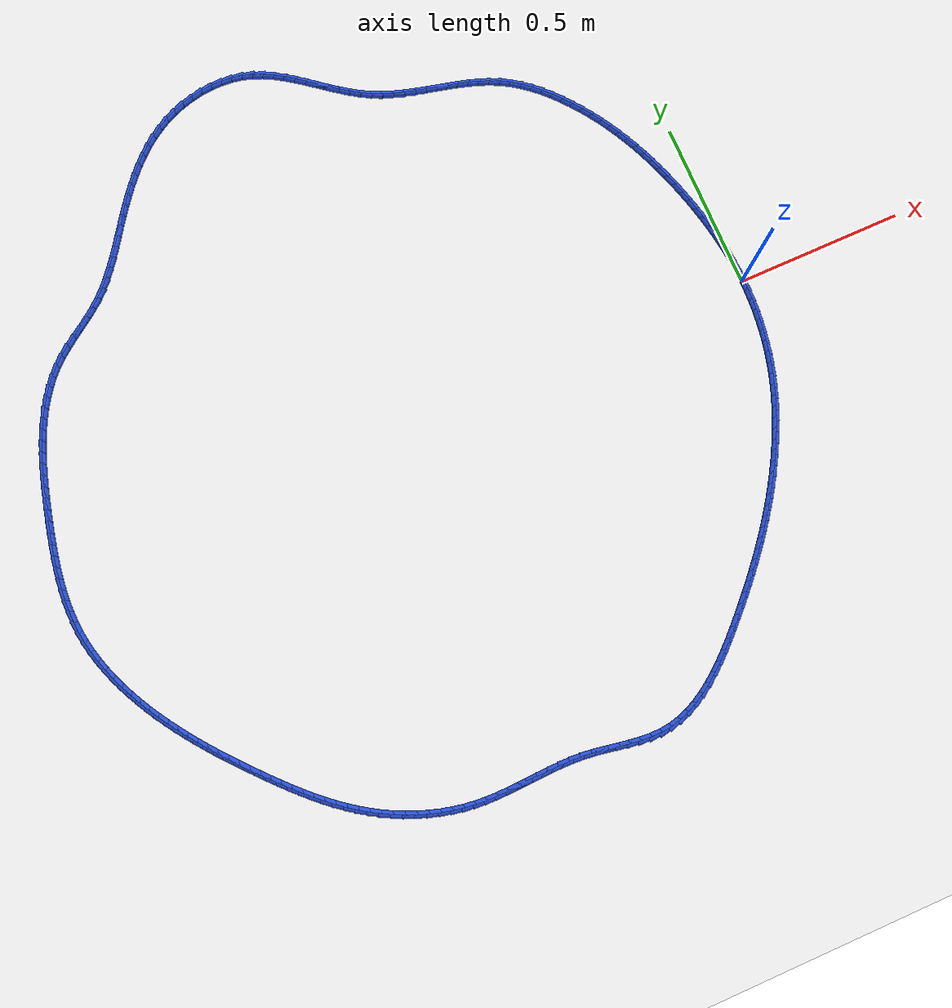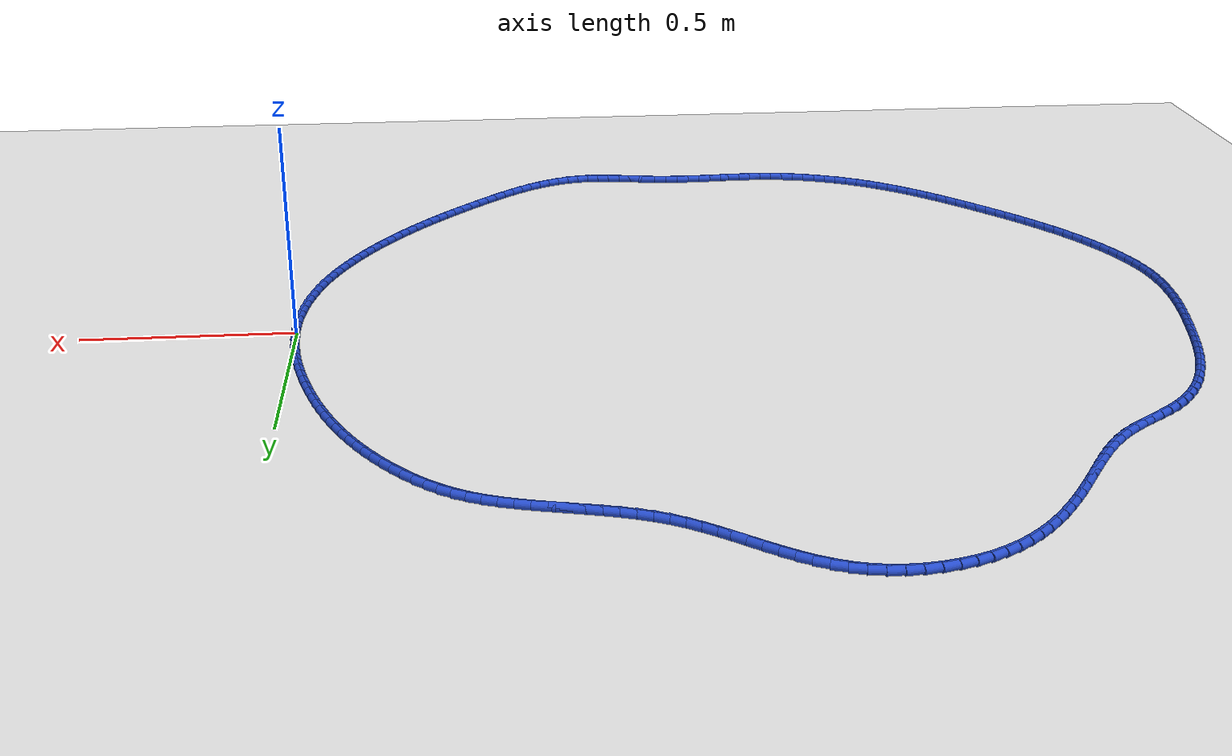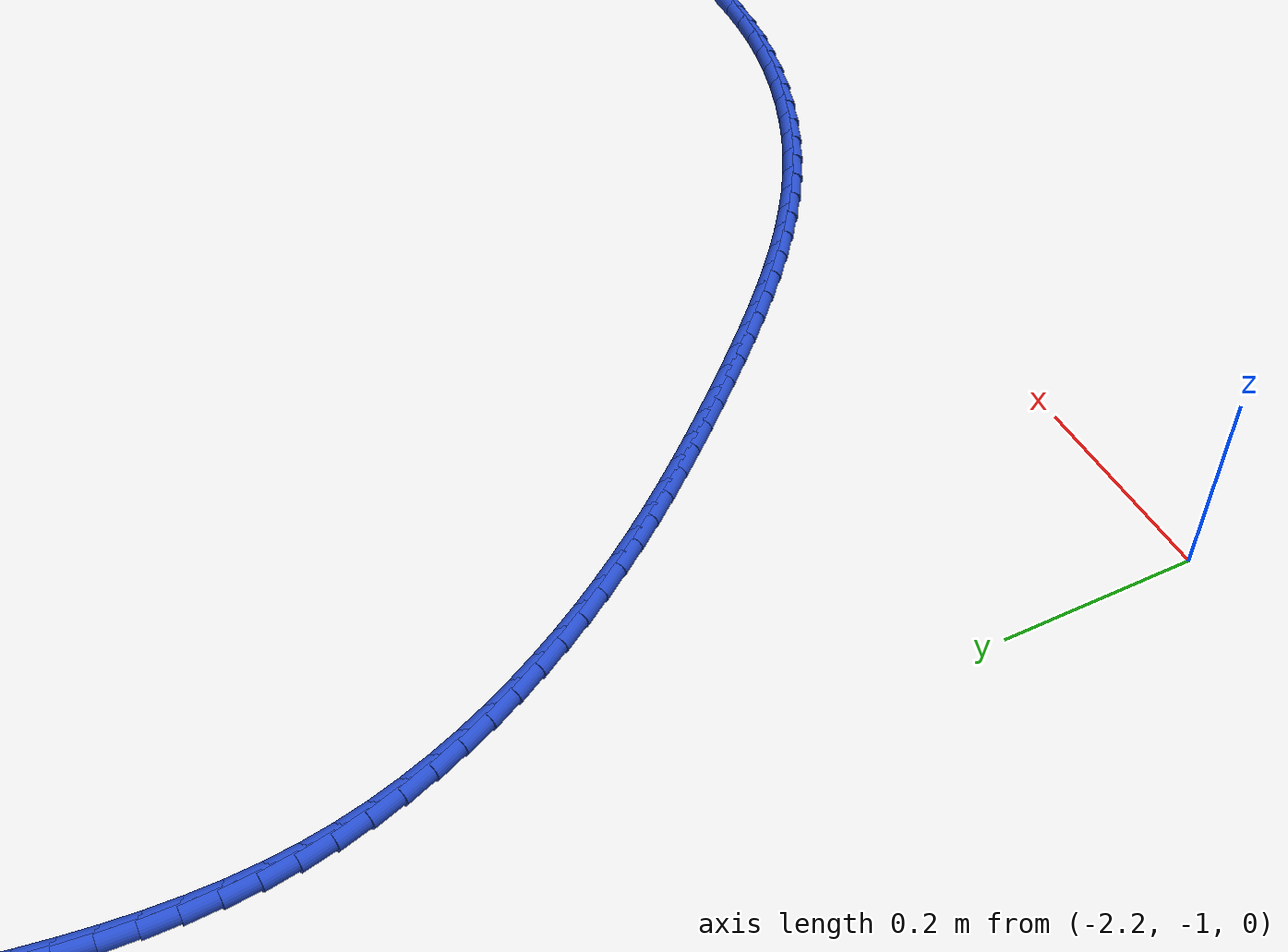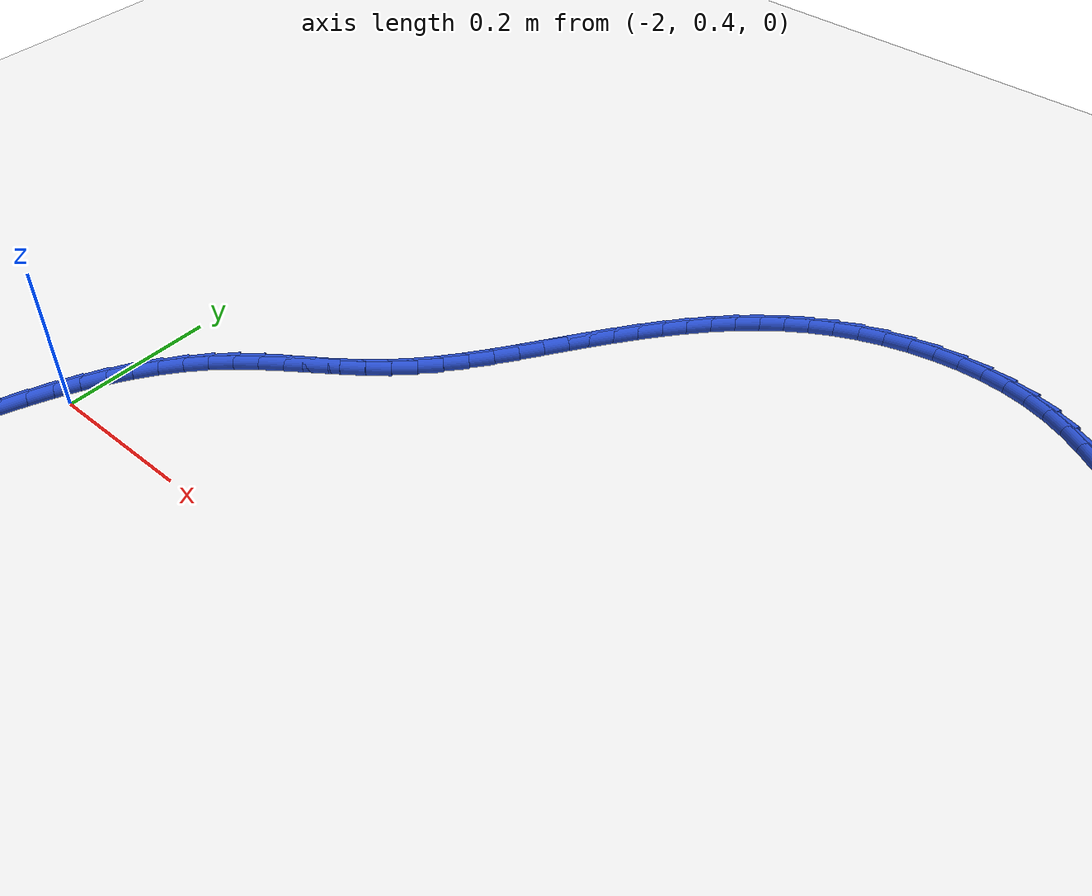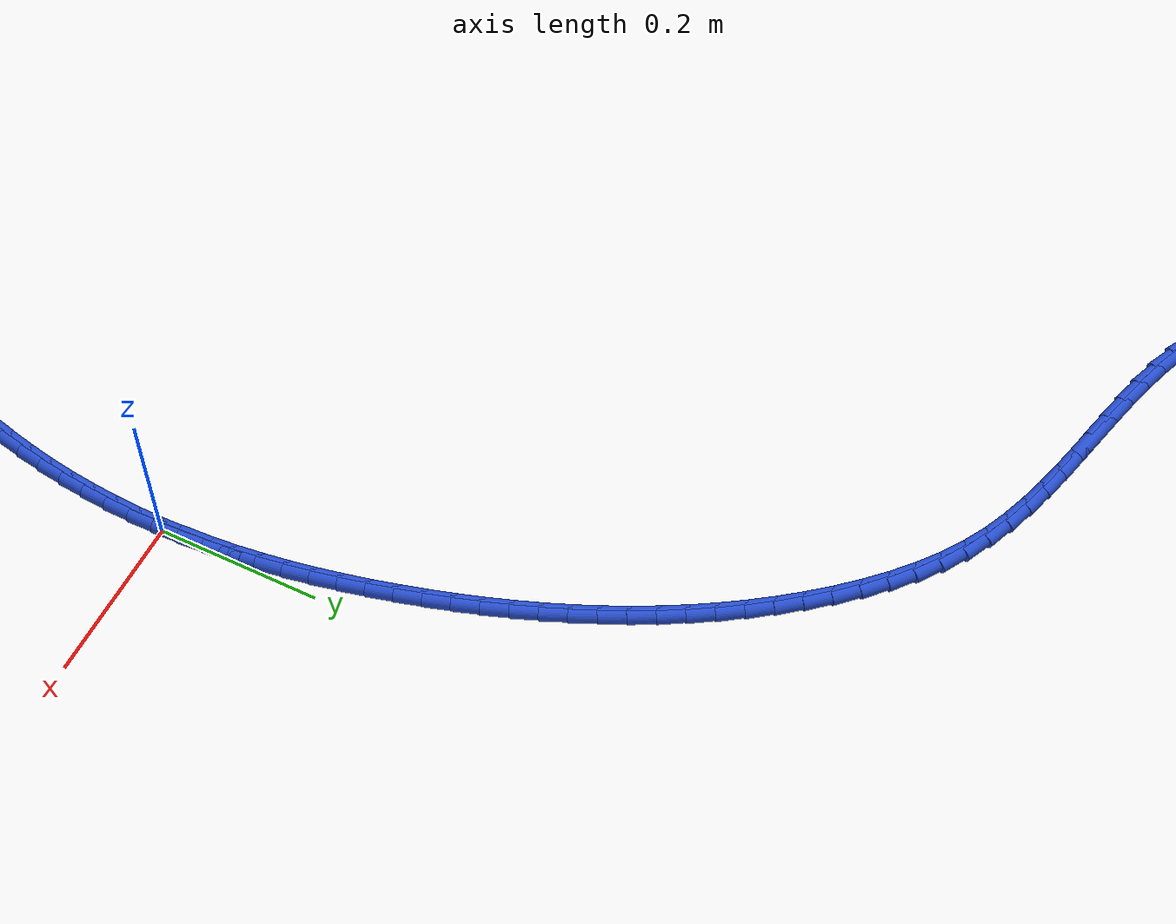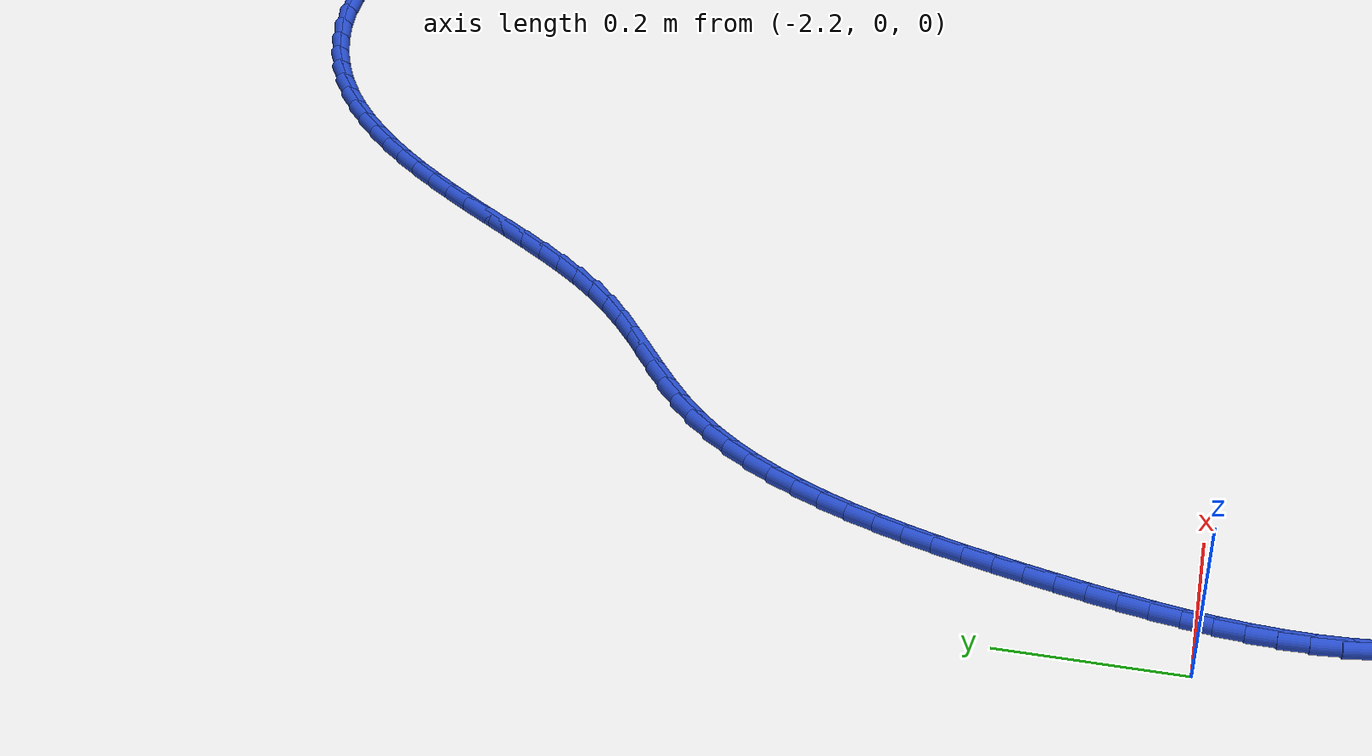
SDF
<sdf version="1.6">
 <world name="default">
  <light name="sun" type="directional">
   <pose>0 0 10 0 -0 0</pose>
   <diffuse>0.8 0.8 0.8 1</diffuse>
   <specular>0.2 0.2 0.2 1</specular>
   <attenuation>
    <range>1000</range>
    <constant>0.9</constant>
    <linear>0.01</linear>
    <quadratic>0.001</quadratic>
   </attenuation>
   <direction>-0.5 0.1 -0.9</direction>
  </light>
  <model name="ground_plane">
   <static>1</static>
   <link name="link">
    <collision name="collision">
     <geometry><plane><normal>0 0 1</normal><size>100 100</size></plane></geometry>
     <surface><friction><ode><mu>100</mu><mu2>50</mu2></ode></friction></surface>
    </collision>
    <visual name="visual">
     <cast_shadows>0</cast_shadows>
     <geometry><plane><normal>0 0 1</normal><size>100 100</size></plane></geometry>
     <material>
      <script><uri>file://media/materials/scripts/gazebo.material</uri><name>Gazebo/WhiteGlow</name></script>
     </material>
    </visual>
   </link>
  </model>
  <gravity>0 0 -9.8</gravity>
  <magnetic_field>6e-06 2.3e-05 -4.2e-05</magnetic_field>
  <atmosphere type="adiabatic"/>
  <physics name="default_physics" default="0" type="ode">
   <max_step_size>0.001</max_step_size>
   <real_time_factor>1</real_time_factor>
   <real_time_update_rate>1000</real_time_update_rate>
  </physics>
  <scene><ambient>0.4 0.4 0.4 1</ambient><background>0.7 0.7 0.7 1</background><shadows>1</shadows></scene>
  <spherical_coordinates>
   <surface_model>EARTH_WGS84</surface_model>
   <latitude_deg>0</latitude_deg>
   <longitude_deg>0</longitude_deg>
   <elevation>0</elevation>
   <heading_deg>0</heading_deg>
  </spherical_coordinates>
  <model name="line">
   <link name="link_0">
    <pose>-8.673617379884035e-19 6.938893903907228e-18 0.01 0 1.57 -1.543074428844468</pose>
    <collision name="collision">
     <geometry><cylinder><radius>0.01</radius><length>0.08</length></cylinder></geometry>
    </collision>
    <visual name="visual">
     <material>
      <script><name>Gazebo/Blue</name><uri>file://media/materials/scripts/gazebo.material</uri></script>
     </material>
     <geometry><cylinder><radius>0.01</radius><length>0.08</length></cylinder></geometry>
    </visual>
   </link>
   <link name="link_1">
    <pose>-0.0008950172281808408 0.03227729729658933 0.01 0 1.57 -1.5096333956772543</pose>
    <collision name="collision">
     <geometry><cylinder><radius>0.01</radius><length>0.08</length></cylinder></geometry>
    </collision>
    <visual name="visual">
     <material>
      <script><name>Gazebo/Blue</name><uri>file://media/materials/scripts/gazebo.material</uri></script>
     </material>
     <geometry><cylinder><radius>0.01</radius><length>0.08</length></cylinder></geometry>
    </visual>
   </link>
   <link name="link_2">
    <pose>-0.0028680352693637506 0.06449545788700523 0.01 0 1.57 -1.4777928060245455</pose>
    <collision name="collision">
     <geometry><cylinder><radius>0.01</radius><length>0.08</length></cylinder></geometry>
    </collision>
    <visual name="visual">
     <material>
      <script><name>Gazebo/Blue</name><uri>file://media/materials/scripts/gazebo.material</uri></script>
     </material>
     <geometry><cylinder><radius>0.01</radius><length>0.08</length></cylinder></geometry>
    </visual>
   </link>
   <link name="link_3">
    <pose>-0.005866550146717172 0.09664332164781306 0.01 0 1.57 -1.447571242681632</pose>
    <collision name="collision">
     <geometry><cylinder><radius>0.01</radius><length>0.08</length></cylinder></geometry>
    </collision>
    <visual name="visual">
     <material>
      <script><name>Gazebo/Blue</name><uri>file://media/materials/scripts/gazebo.material</uri></script>
     </material>
     <geometry><cylinder><radius>0.01</radius><length>0.08</length></cylinder></geometry>
    </visual>
   </link>
   <link name="link_4">
    <pose>-0.00983805788340953 0.1287097284555783 0.01 0 1.57 -1.4189734854219613</pose>
    <collision name="collision">
     <geometry><cylinder><radius>0.01</radius><length>0.08</length></cylinder></geometry>
    </collision>
    <visual name="visual">
     <material>
      <script><name>Gazebo/Blue</name><uri>file://media/materials/scripts/gazebo.material</uri></script>
     </material>
     <geometry><cylinder><radius>0.01</radius><length>0.08</length></cylinder></geometry>
    </visual>
   </link>
   <link name="link_5">
    <pose>-0.014730054502609264 0.16068351818686633 0.01 0 1.57 -1.3919929196407517</pose>
    <collision name="collision">
     <geometry><cylinder><radius>0.01</radius><length>0.08</length></cylinder></geometry>
    </collision>
    <visual name="visual">
     <material>
      <script><name>Gazebo/Blue</name><uri>file://media/materials/scripts/gazebo.material</uri></script>
     </material>
     <geometry><cylinder><radius>0.01</radius><length>0.08</length></cylinder></geometry>
    </visual>
   </link>
   <link name="link_6">
    <pose>-0.02049003602748481 0.19255353071824263 0.01 0 1.57 -1.3666138655909075</pose>
    <collision name="collision">
     <geometry><cylinder><radius>0.01</radius><length>0.08</length></cylinder></geometry>
    </collision>
    <visual name="visual">
     <material>
      <script><name>Gazebo/Blue</name><uri>file://media/materials/scripts/gazebo.material</uri></script>
     </material>
     <geometry><cylinder><radius>0.01</radius><length>0.08</length></cylinder></geometry>
    </visual>
   </link>
   <link name="link_7">
    <pose>-0.0270654984812046 0.22430860592627264 0.01 0 1.57 -1.3428137571653331</pose>
    <collision name="collision">
     <geometry><cylinder><radius>0.01</radius><length>0.08</length></cylinder></geometry>
    </collision>
    <visual name="visual">
     <material>
      <script><name>Gazebo/Blue</name><uri>file://media/materials/scripts/gazebo.material</uri></script>
     </material>
     <geometry><cylinder><radius>0.01</radius><length>0.08</length></cylinder></geometry>
    </visual>
   </link>
   <link name="link_8">
    <pose>-0.034403937886937054 0.25593758368752173 0.01 0 1.57 -1.320565127064045</pose>
    <collision name="collision">
     <geometry><cylinder><radius>0.01</radius><length>0.08</length></cylinder></geometry>
    </collision>
    <visual name="visual">
     <material>
      <script><name>Gazebo/Blue</name><uri>file://media/materials/scripts/gazebo.material</uri></script>
     </material>
     <geometry><cylinder><radius>0.01</radius><length>0.08</length></cylinder></geometry>
    </visual>
   </link>
   <link name="link_9">
    <pose>-0.04245285026785062 0.2874293038785555 0.01 0 1.57 -1.2996378656930734</pose>
    <collision name="collision">
     <geometry><cylinder><radius>0.01</radius><length>0.08</length></cylinder></geometry>
    </collision>
    <visual name="visual">
     <material>
      <script><name>Gazebo/Blue</name><uri>file://media/materials/scripts/gazebo.material</uri></script>
     </material>
     <geometry><cylinder><radius>0.01</radius><length>0.08</length></cylinder></geometry>
    </visual>
   </link>
   <link name="link_10">
    <pose>-0.05116590557504904 0.3187705834602469 0.01 0 1.57 -1.2783561287678809</pose>
    <collision name="collision">
     <geometry><cylinder><radius>0.01</radius><length>0.08</length></cylinder></geometry>
    </collision>
    <visual name="visual">
     <material>
      <script><name>Gazebo/Blue</name><uri>file://media/materials/scripts/gazebo.material</uri></script>
     </material>
     <geometry><cylinder><radius>0.01</radius><length>0.08</length></cylinder></geometry>
    </visual>
   </link>
   <link name="link_11">
    <pose>-0.06054761636015926 0.34993158058314355 0.01 0 1.57 -1.2558774295632977</pose>
    <collision name="collision">
     <geometry><cylinder><radius>0.01</radius><length>0.08</length></cylinder></geometry>
    </collision>
    <visual name="visual">
     <material>
      <script><name>Gazebo/Blue</name><uri>file://media/materials/scripts/gazebo.material</uri></script>
     </material>
     <geometry><cylinder><radius>0.01</radius><length>0.08</length></cylinder></geometry>
    </visual>
   </link>
   <link name="link_12">
    <pose>-0.0706274959015604 0.38087426179546213 0.01 0 1.57 -1.2321620871713928</pose>
    <collision name="collision">
     <geometry><cylinder><radius>0.01</radius><length>0.08</length></cylinder></geometry>
    </collision>
    <visual name="visual">
     <material>
      <script><name>Gazebo/Blue</name><uri>file://media/materials/scripts/gazebo.material</uri></script>
     </material>
     <geometry><cylinder><radius>0.01</radius><length>0.08</length></cylinder></geometry>
    </visual>
   </link>
   <link name="link_13">
    <pose>-0.08143523141045743 0.4115605366555343 0.01 0 1.57 -1.2071777838790654</pose>
    <collision name="collision">
     <geometry><cylinder><radius>0.01</radius><length>0.08</length></cylinder></geometry>
    </collision>
    <visual name="visual">
     <material>
      <script><name>Gazebo/Blue</name><uri>file://media/materials/scripts/gazebo.material</uri></script>
     </material>
     <geometry><cylinder><radius>0.01</radius><length>0.08</length></cylinder></geometry>
    </visual>
   </link>
   <link name="link_14">
    <pose>-0.09300051009805532 0.4419523147216919 0.01 0 1.57 -1.1808950570090266</pose>
    <collision name="collision">
     <geometry><cylinder><radius>0.01</radius><length>0.08</length></cylinder></geometry>
    </collision>
    <visual name="visual">
     <material>
      <script><name>Gazebo/Blue</name><uri>file://media/materials/scripts/gazebo.material</uri></script>
     </material>
     <geometry><cylinder><radius>0.01</radius><length>0.08</length></cylinder></geometry>
    </visual>
   </link>
   <link name="link_15">
    <pose>-0.10535301917555896 0.47201150555226606 0.01 0 1.57 -1.153288567595181</pose>
    <collision name="collision">
     <geometry><cylinder><radius>0.01</radius><length>0.08</length></cylinder></geometry>
    </collision>
    <visual name="visual">
     <material>
      <script><name>Gazebo/Blue</name><uri>file://media/materials/scripts/gazebo.material</uri></script>
     </material>
     <geometry><cylinder><radius>0.01</radius><length>0.08</length></cylinder></geometry>
    </visual>
   </link>
   <link name="link_16">
    <pose>-0.11852244585417335 0.5017000187055887 0.01 0 1.57 -1.1243385240954376</pose>
    <collision name="collision">
     <geometry><cylinder><radius>0.01</radius><length>0.08</length></cylinder></geometry>
    </collision>
    <visual name="visual">
     <material>
      <script><name>Gazebo/Blue</name><uri>file://media/materials/scripts/gazebo.material</uri></script>
     </material>
     <geometry><cylinder><radius>0.01</radius><length>0.08</length></cylinder></geometry>
    </visual>
   </link>
   <link name="link_17">
    <pose>-0.1325384773451034 0.5309797637399915 0.01 0 1.57 -1.09403224947397</pose>
    <collision name="collision">
     <geometry><cylinder><radius>0.01</radius><length>0.08</length></cylinder></geometry>
    </collision>
    <visual name="visual">
     <material>
      <script><name>Gazebo/Blue</name><uri>file://media/materials/scripts/gazebo.material</uri></script>
     </material>
     <geometry><cylinder><radius>0.01</radius><length>0.08</length></cylinder></geometry>
    </visual>
   </link>
   <link name="link_18">
    <pose>-0.14743080085955415 0.5598126502138061 0.01 0 1.57 -1.0623658662460087</pose>
    <collision name="collision">
     <geometry><cylinder><radius>0.01</radius><length>0.08</length></cylinder></geometry>
    </collision>
    <visual name="visual">
     <material>
      <script><name>Gazebo/Blue</name><uri>file://media/materials/scripts/gazebo.material</uri></script>
     </material>
     <geometry><cylinder><radius>0.01</radius><length>0.08</length></cylinder></geometry>
    </visual>
   </link>
   <link name="link_19">
    <pose>-0.16322910360873055 0.5881605876853642 0.01 0 1.57 -1.0293460573031858</pose>
    <collision name="collision">
     <geometry><cylinder><radius>0.01</radius><length>0.08</length></cylinder></geometry>
    </collision>
    <visual name="visual">
     <material>
      <script><name>Gazebo/Blue</name><uri>file://media/materials/scripts/gazebo.material</uri></script>
     </material>
     <geometry><cylinder><radius>0.01</radius><length>0.08</length></cylinder></geometry>
    </visual>
   </link>
   <link name="link_20">
    <pose>-0.17996307280383744 0.6159854857129972 0.01 0 1.57 -0.9949918411005917</pose>
    <collision name="collision">
     <geometry><cylinder><radius>0.01</radius><length>0.08</length></cylinder></geometry>
    </collision>
    <visual name="visual">
     <material>
      <script><name>Gazebo/Blue</name><uri>file://media/materials/scripts/gazebo.material</uri></script>
     </material>
     <geometry><cylinder><radius>0.01</radius><length>0.08</length></cylinder></geometry>
    </visual>
   </link>
   <link name="link_21">
    <pose>-0.19766239565607988 0.643249253855037 0.01 0 1.57 -0.9593362793171075</pose>
    <collision name="collision">
     <geometry><cylinder><radius>0.01</radius><length>0.08</length></cylinder></geometry>
    </collision>
    <visual name="visual">
     <material>
      <script><name>Gazebo/Blue</name><uri>file://media/materials/scripts/gazebo.material</uri></script>
     </material>
     <geometry><cylinder><radius>0.01</radius><length>0.08</length></cylinder></geometry>
    </visual>
   </link>
   <link name="link_22">
    <pose>-0.21635675937666282 0.669913801669815 0.01 0 1.57 -0.9224280154016387</pose>
    <collision name="collision">
     <geometry><cylinder><radius>0.01</radius><length>0.08</length></cylinder></geometry>
    </collision>
    <visual name="visual">
     <material>
      <script><name>Gazebo/Blue</name><uri>file://media/materials/scripts/gazebo.material</uri></script>
     </material>
     <geometry><cylinder><radius>0.01</radius><length>0.08</length></cylinder></geometry>
    </visual>
   </link>
   <link name="link_23">
    <pose>-0.23607585117679114 0.695941038715663 0.01 0 1.57 -0.8841942127554209</pose>
    <collision name="collision">
     <geometry><cylinder><radius>0.01</radius><length>0.08</length></cylinder></geometry>
    </collision>
    <visual name="visual">
     <material>
      <script><name>Gazebo/Blue</name><uri>file://media/materials/scripts/gazebo.material</uri></script>
     </material>
     <geometry><cylinder><radius>0.01</radius><length>0.08</length></cylinder></geometry>
    </visual>
   </link>
   <link name="link_24">
    <pose>-0.2568493046668854 0.7212856577965792 0.01 0 1.57 -0.8420285285298341</pose>
    <collision name="collision">
     <geometry><cylinder><radius>0.01</radius><length>0.08</length></cylinder></geometry>
    </collision>
    <visual name="visual">
     <material>
      <script><name>Gazebo/Blue</name><uri>file://media/materials/scripts/gazebo.material</uri></script>
     </material>
     <geometry><cylinder><radius>0.01</radius><length>0.08</length></cylinder></geometry>
    </visual>
   </link>
   <link name="link_25">
    <pose>-0.27870576432729105 0.7457691762635011 0.01 0 1.57 -0.7931644576735281</pose>
    <collision name="collision">
     <geometry><cylinder><radius>0.01</radius><length>0.08</length></cylinder></geometry>
    </collision>
    <visual name="visual">
     <material>
      <script><name>Gazebo/Blue</name><uri>file://media/materials/scripts/gazebo.material</uri></script>
     </material>
     <geometry><cylinder><radius>0.01</radius><length>0.08</length></cylinder></geometry>
    </visual>
   </link>
   <link name="link_26">
    <pose>-0.30167300449786566 0.7690959566495658 0.01 0 1.57 -0.7368165278572465</pose>
    <collision name="collision">
     <geometry><cylinder><radius>0.01</radius><length>0.08</length></cylinder></geometry>
    </collision>
    <visual name="visual">
     <material>
      <script><name>Gazebo/Blue</name><uri>file://media/materials/scripts/gazebo.material</uri></script>
     </material>
     <geometry><cylinder><radius>0.01</radius><length>0.08</length></cylinder></geometry>
    </visual>
   </link>
   <link name="link_27">
    <pose>-0.3257787698382209 0.7909663653702165 0.01 0 1.57 -0.6722454013185253</pose>
    <collision name="collision">
     <geometry><cylinder><radius>0.01</radius><length>0.08</length></cylinder></geometry>
    </collision>
    <visual name="visual">
     <material>
      <script><name>Gazebo/Blue</name><uri>file://media/materials/scripts/gazebo.material</uri></script>
     </material>
     <geometry><cylinder><radius>0.01</radius><length>0.08</length></cylinder></geometry>
    </visual>
   </link>
   <link name="link_28">
    <pose>-0.3510508050079685 0.8110807688408971 0.01 0 1.57 -0.5987729725593101</pose>
    <collision name="collision">
     <geometry><cylinder><radius>0.01</radius><length>0.08</length></cylinder></geometry>
    </collision>
    <visual name="visual">
     <material>
      <script><name>Gazebo/Blue</name><uri>file://media/materials/scripts/gazebo.material</uri></script>
     </material>
     <geometry><cylinder><radius>0.01</radius><length>0.08</length></cylinder></geometry>
    </visual>
   </link>
   <link name="link_29">
    <pose>-0.37751685466671964 0.8291395334770513 0.01 0 1.57 -0.5163343591205413</pose>
    <collision name="collision">
     <geometry><cylinder><radius>0.01</radius><length>0.08</length></cylinder></geometry>
    </collision>
    <visual name="visual">
     <material>
      <script><name>Gazebo/Blue</name><uri>file://media/materials/scripts/gazebo.material</uri></script>
     </material>
     <geometry><cylinder><radius>0.01</radius><length>0.08</length></cylinder></geometry>
    </visual>
   </link>
   <link name="link_30">
    <pose>-0.4052007445364867 0.8448558069188962 0.01 0 1.57 -0.43539038235903105</pose>
    <collision name="collision">
     <geometry><cylinder><radius>0.01</radius><length>0.08</length></cylinder></geometry>
    </collision>
    <visual name="visual">
     <material>
      <script><name>Gazebo/Blue</name><uri>file://media/materials/scripts/gazebo.material</uri></script>
     </material>
     <geometry><cylinder><radius>0.01</radius><length>0.08</length></cylinder></geometry>
    </visual>
   </link>
   <link name="link_31">
    <pose>-0.4340275169077495 0.8582649091327313 0.01 0 1.57 -0.367697042779744</pose>
    <collision name="collision">
     <geometry><cylinder><radius>0.01</radius><length>0.08</length></cylinder></geometry>
    </collision>
    <visual name="visual">
     <material>
      <script><name>Gazebo/Blue</name><uri>file://media/materials/scripts/gazebo.material</uri></script>
     </material>
     <geometry><cylinder><radius>0.01</radius><length>0.08</length></cylinder></geometry>
    </visual>
   </link>
   <link name="link_32">
    <pose>-0.4638183731370973 0.869740826951312 0.01 0 1.57 -0.31414786341790646</pose>
    <collision name="collision">
     <geometry><cylinder><radius>0.01</radius><length>0.08</length></cylinder></geometry>
    </collision>
    <visual name="visual">
     <material>
      <script><name>Gazebo/Blue</name><uri>file://media/materials/scripts/gazebo.material</uri></script>
     </material>
     <geometry><cylinder><radius>0.01</radius><length>0.08</length></cylinder></geometry>
    </visual>
   </link>
   <link name="link_33">
    <pose>-0.4943895833524727 0.8796736299186203 0.01 0 1.57 -0.2745778383771173</pose>
    <collision name="collision">
     <geometry><cylinder><radius>0.01</radius><length>0.08</length></cylinder></geometry>
    </collision>
    <visual name="visual">
     <material>
      <script><name>Gazebo/Blue</name><uri>file://media/materials/scripts/gazebo.material</uri></script>
     </material>
     <geometry><cylinder><radius>0.01</radius><length>0.08</length></cylinder></geometry>
    </visual>
   </link>
   <link name="link_34">
    <pose>-0.5255574176818177 0.8884533875786376 0.01 0 1.57 -0.24859931215305123</pose>
    <collision name="collision">
     <geometry><cylinder><radius>0.01</radius><length>0.08</length></cylinder></geometry>
    </collision>
    <visual name="visual">
     <material>
      <script><name>Gazebo/Blue</name><uri>file://media/materials/scripts/gazebo.material</uri></script>
     </material>
     <geometry><cylinder><radius>0.01</radius><length>0.08</length></cylinder></geometry>
    </visual>
   </link>
   <link name="link_35">
    <pose>-0.5571381462530762 0.8964701694753467 0.01 0 1.57 -0.2358273862545495</pose>
    <collision name="collision">
     <geometry><cylinder><radius>0.01</radius><length>0.08</length></cylinder></geometry>
    </collision>
    <visual name="visual">
     <material>
      <script><name>Gazebo/Blue</name><uri>file://media/materials/scripts/gazebo.material</uri></script>
     </material>
     <geometry><cylinder><radius>0.01</radius><length>0.08</length></cylinder></geometry>
    </visual>
   </link>
   <link name="link_36">
    <pose>-0.5889480391941898 0.9041140451527288 0.01 0 1.57 -0.23601273243932025</pose>
    <collision name="collision">
     <geometry><cylinder><radius>0.01</radius><length>0.08</length></cylinder></geometry>
    </collision>
    <visual name="visual">
     <material>
      <script><name>Gazebo/Blue</name><uri>file://media/materials/scripts/gazebo.material</uri></script>
     </material>
     <geometry><cylinder><radius>0.01</radius><length>0.08</length></cylinder></geometry>
    </visual>
   </link>
   <link name="link_37">
    <pose>-0.6208033666331018 0.9117750841547666 0.01 0 1.57 -0.24909951020728224</pose>
    <collision name="collision">
     <geometry><cylinder><radius>0.01</radius><length>0.08</length></cylinder></geometry>
    </collision>
    <visual name="visual">
     <material>
      <script><name>Gazebo/Blue</name><uri>file://media/materials/scripts/gazebo.material</uri></script>
     </material>
     <geometry><cylinder><radius>0.01</radius><length>0.08</length></cylinder></geometry>
    </visual>
   </link>
   <link name="link_38">
    <pose>-0.6525203986977548 0.9198433560254419 0.01 0 1.57 -0.27522175141478333</pose>
    <collision name="collision">
     <geometry><cylinder><radius>0.01</radius><length>0.08</length></cylinder></geometry>
    </collision>
    <visual name="visual">
     <material>
      <script><name>Gazebo/Blue</name><uri>file://media/materials/scripts/gazebo.material</uri></script>
     </material>
     <geometry><cylinder><radius>0.01</radius><length>0.08</length></cylinder></geometry>
    </visual>
   </link>
   <link name="link_39">
    <pose>-0.6839154055160909 0.9287089303087362 0.01 0 1.57 -0.3146400045188415</pose>
    <collision name="collision">
     <geometry><cylinder><radius>0.01</radius><length>0.08</length></cylinder></geometry>
    </collision>
    <visual name="visual">
     <material>
      <script><name>Gazebo/Blue</name><uri>file://media/materials/scripts/gazebo.material</uri></script>
     </material>
     <geometry><cylinder><radius>0.01</radius><length>0.08</length></cylinder></geometry>
    </visual>
   </link>
   <link name="link_40">
    <pose>-0.7148046572160536 0.9387618765486323 0.01 0 1.57 -0.3676091250936983</pose>
    <collision name="collision">
     <geometry><cylinder><radius>0.01</radius><length>0.08</length></cylinder></geometry>
    </collision>
    <visual name="visual">
     <material>
      <script><name>Gazebo/Blue</name><uri>file://media/materials/scripts/gazebo.material</uri></script>
     </material>
     <geometry><cylinder><radius>0.01</radius><length>0.08</length></cylinder></geometry>
    </visual>
   </link>
   <link name="link_41">
    <pose>-0.7450044239255853 0.9503922642891117 0.01 0 1.57 -0.43416515468444045</pose>
    <collision name="collision">
     <geometry><cylinder><radius>0.01</radius><length>0.08</length></cylinder></geometry>
    </collision>
    <visual name="visual">
     <material>
      <script><name>Gazebo/Blue</name><uri>file://media/materials/scripts/gazebo.material</uri></script>
     </material>
     <geometry><cylinder><radius>0.01</radius><length>0.08</length></cylinder></geometry>
    </visual>
   </link>
   <link name="link_42">
    <pose>-0.7743309757726284 0.9639901630741567 0.01 0 1.57 -0.5089399456784874</pose>
    <collision name="collision">
     <geometry><cylinder><radius>0.01</radius><length>0.08</length></cylinder></geometry>
    </collision>
    <visual name="visual">
     <material>
      <script><name>Gazebo/Blue</name><uri>file://media/materials/scripts/gazebo.material</uri></script>
     </material>
     <geometry><cylinder><radius>0.01</radius><length>0.08</length></cylinder></geometry>
    </visual>
   </link>
   <link name="link_43">
    <pose>-0.8026647938310223 0.9797995215825887 0.01 0 1.57 -0.5715035804731994</pose>
    <collision name="collision">
     <geometry><cylinder><radius>0.01</radius><length>0.08</length></cylinder></geometry>
    </collision>
    <visual name="visual">
     <material>
      <script><name>Gazebo/Blue</name><uri>file://media/materials/scripts/gazebo.material</uri></script>
     </material>
     <geometry><cylinder><radius>0.01</radius><length>0.08</length></cylinder></geometry>
    </visual>
   </link>
   <link name="link_44">
    <pose>-0.8301463347246314 0.9974726782660338 0.01 0 1.57 -0.6170683168024339</pose>
    <collision name="collision">
     <geometry><cylinder><radius>0.01</radius><length>0.08</length></cylinder></geometry>
    </collision>
    <visual name="visual">
     <material>
      <script><name>Gazebo/Blue</name><uri>file://media/materials/scripts/gazebo.material</uri></script>
     </material>
     <geometry><cylinder><radius>0.01</radius><length>0.08</length></cylinder></geometry>
    </visual>
   </link>
   <link name="link_45">
    <pose>-0.8569818414294227 1.0165122656568082 0.01 0 1.57 -0.6462078906689612</pose>
    <collision name="collision">
     <geometry><cylinder><radius>0.01</radius><length>0.08</length></cylinder></geometry>
    </collision>
    <visual name="visual">
     <material>
      <script><name>Gazebo/Blue</name><uri>file://media/materials/scripts/gazebo.material</uri></script>
     </material>
     <geometry><cylinder><radius>0.01</radius><length>0.08</length></cylinder></geometry>
    </visual>
   </link>
   <link name="link_46">
    <pose>-0.88337755692565 1.0364209162774782 0.01 0 1.57 -0.6594215010777789</pose>
    <collision name="collision">
     <geometry><cylinder><radius>0.01</radius><length>0.08</length></cylinder></geometry>
    </collision>
    <visual name="visual">
     <material>
      <script><name>Gazebo/Blue</name><uri>file://media/materials/scripts/gazebo.material</uri></script>
     </material>
     <geometry><cylinder><radius>0.01</radius><length>0.08</length></cylinder></geometry>
    </visual>
   </link>
   <link name="link_47">
    <pose>-0.9095397241935659 1.056701262650609 0.01 0 1.57 -0.6569188849797652</pose>
    <collision name="collision">
     <geometry><cylinder><radius>0.01</radius><length>0.08</length></cylinder></geometry>
    </collision>
    <visual name="visual">
     <material>
      <script><name>Gazebo/Blue</name><uri>file://media/materials/scripts/gazebo.material</uri></script>
     </material>
     <geometry><cylinder><radius>0.01</radius><length>0.08</length></cylinder></geometry>
    </visual>
   </link>
   <link name="link_48">
    <pose>-0.9356745862134226 1.0768559372987652 0.01 0 1.57 -0.6385279612100464</pose>
    <collision name="collision">
     <geometry><cylinder><radius>0.01</radius><length>0.08</length></cylinder></geometry>
    </collision>
    <visual name="visual">
     <material>
      <script><name>Gazebo/Blue</name><uri>file://media/materials/scripts/gazebo.material</uri></script>
     </material>
     <geometry><cylinder><radius>0.01</radius><length>0.08</length></cylinder></geometry>
    </visual>
   </link>
   <link name="link_49">
    <pose>-0.9619883859654738 1.0963875727445132 0.01 0 1.57 -0.6037020902337749</pose>
    <collision name="collision">
     <geometry><cylinder><radius>0.01</radius><length>0.08</length></cylinder></geometry>
    </collision>
    <visual name="visual">
     <material>
      <script><name>Gazebo/Blue</name><uri>file://media/materials/scripts/gazebo.material</uri></script>
     </material>
     <geometry><cylinder><radius>0.01</radius><length>0.08</length></cylinder></geometry>
    </visual>
   </link>
   <link name="link_50">
    <pose>-0.9886873664299722 1.1147988015104182 0.01 0 1.57 -0.5516379656487751</pose>
    <collision name="collision">
     <geometry><cylinder><radius>0.01</radius><length>0.08</length></cylinder></geometry>
    </collision>
    <visual name="visual">
     <material>
      <script><name>Gazebo/Blue</name><uri>file://media/materials/scripts/gazebo.material</uri></script>
     </material>
     <geometry><cylinder><radius>0.01</radius><length>0.08</length></cylinder></geometry>
    </visual>
   </link>
   <link name="link_51">
    <pose>-1.0159777705871709 1.131592256119046 0.01 0 1.57 -0.4815493712645671</pose>
    <collision name="collision">
     <geometry><cylinder><radius>0.01</radius><length>0.08</length></cylinder></geometry>
    </collision>
    <visual name="visual">
     <material>
      <script><name>Gazebo/Blue</name><uri>file://media/materials/scripts/gazebo.material</uri></script>
     </material>
     <geometry><cylinder><radius>0.01</radius><length>0.08</length></cylinder></geometry>
    </visual>
   </link>
   <link name="link_52">
    <pose>-1.044065841417322 1.146270569092961 0.01 0 1.57 -0.393154085487555</pose>
    <collision name="collision">
     <geometry><cylinder><radius>0.01</radius><length>0.08</length></cylinder></geometry>
    </collision>
    <visual name="visual">
     <material>
      <script><name>Gazebo/Blue</name><uri>file://media/materials/scripts/gazebo.material</uri></script>
     </material>
     <geometry><cylinder><radius>0.01</radius><length>0.08</length></cylinder></geometry>
    </visual>
   </link>
   <link name="link_53">
    <pose>-1.0731578219006797 1.1583363729547302 0.01 0 1.57 -0.2874507101214639</pose>
    <collision name="collision">
     <geometry><cylinder><radius>0.01</radius><length>0.08</length></cylinder></geometry>
    </collision>
    <visual name="visual">
     <material>
      <script><name>Gazebo/Blue</name><uri>file://media/materials/scripts/gazebo.material</uri></script>
     </material>
     <geometry><cylinder><radius>0.01</radius><length>0.08</length></cylinder></geometry>
    </visual>
   </link>
   <link name="link_54">
    <pose>-1.1034581520128592 1.1672943197158536 0.01 0 1.57 -0.17479858856976555</pose>
    <collision name="collision">
     <geometry><cylinder><radius>0.01</radius><length>0.08</length></cylinder></geometry>
    </collision>
    <visual name="visual">
     <material>
      <script><name>Gazebo/Blue</name><uri>file://media/materials/scripts/gazebo.material</uri></script>
     </material>
     <geometry><cylinder><radius>0.01</radius><length>0.08</length></cylinder></geometry>
    </visual>
   </link>
   <link name="link_55">
    <pose>-1.1349816903962433 1.1728614054923485 0.01 0 1.57 -0.07052735428449061</pose>
    <collision name="collision">
     <geometry><cylinder><radius>0.01</radius><length>0.08</length></cylinder></geometry>
    </collision>
    <visual name="visual">
     <material>
      <script><name>Gazebo/Blue</name><uri>file://media/materials/scripts/gazebo.material</uri></script>
     </material>
     <geometry><cylinder><radius>0.01</radius><length>0.08</length></cylinder></geometry>
    </visual>
   </link>
   <link name="link_56">
    <pose>-1.1673895521307445 1.1751508434682247 0.01 0 1.57 0.025261658291936773</pose>
    <collision name="collision">
     <geometry><cylinder><radius>0.01</radius><length>0.08</length></cylinder></geometry>
    </collision>
    <visual name="visual">
     <material>
      <script><name>Gazebo/Blue</name><uri>file://media/materials/scripts/gazebo.material</uri></script>
     </material>
     <geometry><cylinder><radius>0.01</radius><length>0.08</length></cylinder></geometry>
    </visual>
   </link>
   <link name="link_57">
    <pose>-1.2003041562350258 1.1743191890718678 0.01 0 1.57 0.11438228202836787</pose>
    <collision name="collision">
     <geometry><cylinder><radius>0.01</radius><length>0.08</length></cylinder></geometry>
    </collision>
    <visual name="visual">
     <material>
      <script><name>Gazebo/Blue</name><uri>file://media/materials/scripts/gazebo.material</uri></script>
     </material>
     <geometry><cylinder><radius>0.01</radius><length>0.08</length></cylinder></geometry>
    </visual>
   </link>
   <link name="link_58">
    <pose>-1.2333479217277517 1.1705229977316642 0.01 0 1.57 0.19871762019774353</pose>
    <collision name="collision">
     <geometry><cylinder><radius>0.01</radius><length>0.08</length></cylinder></geometry>
    </collision>
    <visual name="visual">
     <material>
      <script><name>Gazebo/Blue</name><uri>file://media/materials/scripts/gazebo.material</uri></script>
     </material>
     <geometry><cylinder><radius>0.01</radius><length>0.08</length></cylinder></geometry>
    </visual>
   </link>
   <link name="link_59">
    <pose>-1.2661432676275846 1.1639188248759984 0.01 0 1.57 0.2801482748937279</pose>
    <collision name="collision">
     <geometry><cylinder><radius>0.01</radius><length>0.08</length></cylinder></geometry>
    </collision>
    <visual name="visual">
     <material>
      <script><name>Gazebo/Blue</name><uri>file://media/materials/scripts/gazebo.material</uri></script>
     </material>
     <geometry><cylinder><radius>0.01</radius><length>0.08</length></cylinder></geometry>
    </visual>
   </link>
   <link name="link_60">
    <pose>-1.29831261295319 1.1546632259332577 0.01 0 1.57 0.36055037854988303</pose>
    <collision name="collision">
     <geometry><cylinder><radius>0.01</radius><length>0.08</length></cylinder></geometry>
    </collision>
    <visual name="visual">
     <material>
      <script><name>Gazebo/Blue</name><uri>file://media/materials/scripts/gazebo.material</uri></script>
     </material>
     <geometry><cylinder><radius>0.01</radius><length>0.08</length></cylinder></geometry>
    </visual>
   </link>
   <link name="link_61">
    <pose>-1.3294783767232297 1.1429127563318269 0.01 0 1.57 0.44181163152796715</pose>
    <collision name="collision">
     <geometry><cylinder><radius>0.01</radius><length>0.08</length></cylinder></geometry>
    </collision>
    <visual name="visual">
     <material>
      <script><name>Gazebo/Blue</name><uri>file://media/materials/scripts/gazebo.material</uri></script>
     </material>
     <geometry><cylinder><radius>0.01</radius><length>0.08</length></cylinder></geometry>
    </visual>
   </link>
   <link name="link_62">
    <pose>-1.3592644331069408 1.1288240836118564 0.01 0 1.57 0.5231185889847798</pose>
    <collision name="collision">
     <geometry><cylinder><radius>0.01</radius><length>0.08</length></cylinder></geometry>
    </collision>
    <visual name="visual">
     <material>
      <script><name>Gazebo/Blue</name><uri>file://media/materials/scripts/gazebo.material</uri></script>
     </material>
     <geometry><cylinder><radius>0.01</radius><length>0.08</length></cylinder></geometry>
    </visual>
   </link>
   <link name="link_63">
    <pose>-1.3874551028551296 1.1125662368860205 0.01 0 1.57 0.5994811732689038</pose>
    <collision name="collision">
     <geometry><cylinder><radius>0.01</radius><length>0.08</length></cylinder></geometry>
    </collision>
    <visual name="visual">
     <material>
      <script><name>Gazebo/Blue</name><uri>file://media/materials/scripts/gazebo.material</uri></script>
     </material>
     <geometry><cylinder><radius>0.01</radius><length>0.08</length></cylinder></geometry>
    </visual>
   </link>
   <link name="link_64">
    <pose>-1.4141382478238604 1.0943316315264588 0.01 0 1.57 0.6693801383520134</pose>
    <collision name="collision">
     <geometry><cylinder><radius>0.01</radius><length>0.08</length></cylinder></geometry>
    </collision>
    <visual name="visual">
     <material>
      <script><name>Gazebo/Blue</name><uri>file://media/materials/scripts/gazebo.material</uri></script>
     </material>
     <geometry><cylinder><radius>0.01</radius><length>0.08</length></cylinder></geometry>
    </visual>
   </link>
   <link name="link_65">
    <pose>-1.4394355043166307 1.0743152850503819 0.01 0 1.57 0.7322024890332466</pose>
    <collision name="collision">
     <geometry><cylinder><radius>0.01</radius><length>0.08</length></cylinder></geometry>
    </collision>
    <visual name="visual">
     <material>
      <script><name>Gazebo/Blue</name><uri>file://media/materials/scripts/gazebo.material</uri></script>
     </material>
     <geometry><cylinder><radius>0.01</radius><length>0.08</length></cylinder></geometry>
    </visual>
   </link>
   <link name="link_66">
    <pose>-1.463468508636936 1.0527122149749988 0.01 0 1.57 0.7876731367345937</pose>
    <collision name="collision">
     <geometry><cylinder><radius>0.01</radius><length>0.08</length></cylinder></geometry>
    </collision>
    <visual name="visual">
     <material>
      <script><name>Gazebo/Blue</name><uri>file://media/materials/scripts/gazebo.material</uri></script>
     </material>
     <geometry><cylinder><radius>0.01</radius><length>0.08</length></cylinder></geometry>
    </visual>
   </link>
   <link name="link_67">
    <pose>-1.486358897088272 1.0297174388175208 0.01 0 1.57 0.8357682828071806</pose>
    <collision name="collision">
     <geometry><cylinder><radius>0.01</radius><length>0.08</length></cylinder></geometry>
    </collision>
    <visual name="visual">
     <material>
      <script><name>Gazebo/Blue</name><uri>file://media/materials/scripts/gazebo.material</uri></script>
     </material>
     <geometry><cylinder><radius>0.01</radius><length>0.08</length></cylinder></geometry>
    </visual>
   </link>
   <link name="link_68">
    <pose>-1.5082283059741353 1.0055259740951574 0.01 0 1.57 0.8766255502183988</pose>
    <collision name="collision">
     <geometry><cylinder><radius>0.01</radius><length>0.08</length></cylinder></geometry>
    </collision>
    <visual name="visual">
     <material>
      <script><name>Gazebo/Blue</name><uri>file://media/materials/scripts/gazebo.material</uri></script>
     </material>
     <geometry><cylinder><radius>0.01</radius><length>0.08</length></cylinder></geometry>
    </visual>
   </link>
   <link name="link_69">
    <pose>-1.5291983715980224 0.9803328383251187 0.01 0 1.57 0.9104652956956031</pose>
    <collision name="collision">
     <geometry><cylinder><radius>0.01</radius><length>0.08</length></cylinder></geometry>
    </collision>
    <visual name="visual">
     <material>
      <script><name>Gazebo/Blue</name><uri>file://media/materials/scripts/gazebo.material</uri></script>
     </material>
     <geometry><cylinder><radius>0.01</radius><length>0.08</length></cylinder></geometry>
    </visual>
   </link>
   <link name="link_70">
    <pose>-1.5493907302634293 0.9543330490246162 0.01 0 1.57 0.9375285910287304</pose>
    <collision name="collision">
     <geometry><cylinder><radius>0.01</radius><length>0.08</length></cylinder></geometry>
    </collision>
    <visual name="visual">
     <material>
      <script><name>Gazebo/Blue</name><uri>file://media/materials/scripts/gazebo.material</uri></script>
     </material>
     <geometry><cylinder><radius>0.01</radius><length>0.08</length></cylinder></geometry>
    </visual>
   </link>
   <link name="link_71">
    <pose>-1.5689270182738515 0.927721623710859 0.01 0 1.57 0.9580315768626112</pose>
    <collision name="collision">
     <geometry><cylinder><radius>0.01</radius><length>0.08</length></cylinder></geometry>
    </collision>
    <visual name="visual">
     <material>
      <script><name>Gazebo/Blue</name><uri>file://media/materials/scripts/gazebo.material</uri></script>
     </material>
     <geometry><cylinder><radius>0.01</radius><length>0.08</length></cylinder></geometry>
    </visual>
   </link>
   <link name="link_72">
    <pose>-1.5879288719327858 0.9006935799010574 0.01 0 1.57 0.9721211932132059</pose>
    <collision name="collision">
     <geometry><cylinder><radius>0.01</radius><length>0.08</length></cylinder></geometry>
    </collision>
    <visual name="visual">
     <material>
      <script><name>Gazebo/Blue</name><uri>file://media/materials/scripts/gazebo.material</uri></script>
     </material>
     <geometry><cylinder><radius>0.01</radius><length>0.08</length></cylinder></geometry>
    </visual>
   </link>
   <link name="link_73">
    <pose>-1.6065183378968515 0.8734440340795327 0.01 0 1.57 0.9783896076067643</pose>
    <collision name="collision">
     <geometry><cylinder><radius>0.01</radius><length>0.08</length></cylinder></geometry>
    </collision>
    <visual name="visual">
     <material>
      <script><name>Gazebo/Blue</name><uri>file://media/materials/scripts/gazebo.material</uri></script>
     </material>
     <geometry><cylinder><radius>0.01</radius><length>0.08</length></cylinder></geometry>
    </visual>
   </link>
   <link name="link_74">
    <pose>-1.6248681004407655 0.8461803152824333 0.01 0 1.57 0.9738761532393932</pose>
    <collision name="collision">
     <geometry><cylinder><radius>0.01</radius><length>0.08</length></cylinder></geometry>
    </collision>
    <visual name="visual">
     <material>
      <script><name>Gazebo/Blue</name><uri>file://media/materials/scripts/gazebo.material</uri></script>
     </material>
     <geometry><cylinder><radius>0.01</radius><length>0.08</length></cylinder></geometry>
    </visual>
   </link>
   <link name="link_75">
    <pose>-1.6432497238521666 0.8191335999804368 0.01 0 1.57 0.9580685158001965</pose>
    <collision name="collision">
     <geometry><cylinder><radius>0.01</radius><length>0.08</length></cylinder></geometry>
    </collision>
    <visual name="visual">
     <material>
      <script><name>Gazebo/Blue</name><uri>file://media/materials/scripts/gazebo.material</uri></script>
     </material>
     <geometry><cylinder><radius>0.01</radius><length>0.08</length></cylinder></geometry>
    </visual>
   </link>
   <link name="link_76">
    <pose>-1.6619462080156817 0.792537822629809 0.01 0 1.57 0.9307332477358957</pose>
    <collision name="collision">
     <geometry><cylinder><radius>0.01</radius><length>0.08</length></cylinder></geometry>
    </collision>
    <visual name="visual">
     <material>
      <script><name>Gazebo/Blue</name><uri>file://media/materials/scripts/gazebo.material</uri></script>
     </material>
     <geometry><cylinder><radius>0.01</radius><length>0.08</length></cylinder></geometry>
    </visual>
   </link>
   <link name="link_77">
    <pose>-1.6812405528159375 0.7666269176868151 0.01 0 1.57 0.8916421656154006</pose>
    <collision name="collision">
     <geometry><cylinder><radius>0.01</radius><length>0.08</length></cylinder></geometry>
    </collision>
    <visual name="visual">
     <material>
      <script><name>Gazebo/Blue</name><uri>file://media/materials/scripts/gazebo.material</uri></script>
     </material>
     <geometry><cylinder><radius>0.01</radius><length>0.08</length></cylinder></geometry>
    </visual>
   </link>
   <link name="link_78">
    <pose>-1.7014157581375609 0.741634819607721 0.01 0 1.57 0.8406843584865529</pose>
    <collision name="collision">
     <geometry><cylinder><radius>0.01</radius><length>0.08</length></cylinder></geometry>
    </collision>
    <visual name="visual">
     <material>
      <script><name>Gazebo/Blue</name><uri>file://media/materials/scripts/gazebo.material</uri></script>
     </material>
     <geometry><cylinder><radius>0.01</radius><length>0.08</length></cylinder></geometry>
    </visual>
   </link>
   <link name="link_79">
    <pose>-1.722754823865179 0.7177954628487917 0.01 0 1.57 0.7780319107576059</pose>
    <collision name="collision">
     <geometry><cylinder><radius>0.01</radius><length>0.08</length></cylinder></geometry>
    </collision>
    <visual name="visual">
     <material>
      <script><name>Gazebo/Blue</name><uri>file://media/materials/scripts/gazebo.material</uri></script>
     </material>
     <geometry><cylinder><radius>0.01</radius><length>0.08</length></cylinder></geometry>
    </visual>
   </link>
   <link name="link_80">
    <pose>-1.7455407498834195 0.6953427818662934 0.01 0 1.57 0.7081023459111364</pose>
    <collision name="collision">
     <geometry><cylinder><radius>0.01</radius><length>0.08</length></cylinder></geometry>
    </collision>
    <visual name="visual">
     <material>
      <script><name>Gazebo/Blue</name><uri>file://media/materials/scripts/gazebo.material</uri></script>
     </material>
     <geometry><cylinder><radius>0.01</radius><length>0.08</length></cylinder></geometry>
    </visual>
   </link>
   <link name="link_81">
    <pose>-1.7699647760100492 0.6744300901823261 0.01 0 1.57 0.6545696513120449</pose>
    <collision name="collision">
     <geometry><cylinder><radius>0.01</radius><length>0.08</length></cylinder></geometry>
    </collision>
    <visual name="visual">
     <material>
      <script><name>Gazebo/Blue</name><uri>file://media/materials/scripts/gazebo.material</uri></script>
     </material>
     <geometry><cylinder><radius>0.01</radius><length>0.08</length></cylinder></geometry>
    </visual>
   </link>
   <link name="link_82">
    <pose>-1.7956540650638966 0.6547150999517265 0.01 0 1.57 0.6255986368360611</pose>
    <collision name="collision">
     <geometry><cylinder><radius>0.01</radius><length>0.08</length></cylinder></geometry>
    </collision>
    <visual name="visual">
     <material>
      <script><name>Gazebo/Blue</name><uri>file://media/materials/scripts/gazebo.material</uri></script>
     </material>
     <geometry><cylinder><radius>0.01</radius><length>0.08</length></cylinder></geometry>
    </visual>
   </link>
   <link name="link_83">
    <pose>-1.8220215866670624 0.635667331927526 0.01 0 1.57 0.6205645698747805</pose>
    <collision name="collision">
     <geometry><cylinder><radius>0.01</radius><length>0.08</length></cylinder></geometry>
    </collision>
    <visual name="visual">
     <material>
      <script><name>Gazebo/Blue</name><uri>file://media/materials/scripts/gazebo.material</uri></script>
     </material>
     <geometry><cylinder><radius>0.01</radius><length>0.08</length></cylinder></geometry>
    </visual>
   </link>
   <link name="link_84">
    <pose>-1.8484798985308575 0.616755944955515 0.01 0 1.57 0.6394112817374145</pose>
    <collision name="collision">
     <geometry><cylinder><radius>0.01</radius><length>0.08</length></cylinder></geometry>
    </collision>
    <visual name="visual">
     <material>
      <script><name>Gazebo/Blue</name><uri>file://media/materials/scripts/gazebo.material</uri></script>
     </material>
     <geometry><cylinder><radius>0.01</radius><length>0.08</length></cylinder></geometry>
    </visual>
   </link>
   <link name="link_85">
    <pose>-1.874441558366595 0.597450097881485 0.01 0 1.57 0.6827552861111479</pose>
    <collision name="collision">
     <geometry><cylinder><radius>0.01</radius><length>0.08</length></cylinder></geometry>
    </collision>
    <visual name="visual">
     <material>
      <script><name>Gazebo/Blue</name><uri>file://media/materials/scripts/gazebo.material</uri></script>
     </material>
     <geometry><cylinder><radius>0.01</radius><length>0.08</length></cylinder></geometry>
    </visual>
   </link>
   <link name="link_86">
    <pose>-1.8993191238855862 0.5772189495512272 0.01 0 1.57 0.7508582629793781</pose>
    <collision name="collision">
     <geometry><cylinder><radius>0.01</radius><length>0.08</length></cylinder></geometry>
    </collision>
    <visual name="visual">
     <material>
      <script><name>Gazebo/Blue</name><uri>file://media/materials/scripts/gazebo.material</uri></script>
     </material>
     <geometry><cylinder><radius>0.01</radius><length>0.08</length></cylinder></geometry>
    </visual>
   </link>
   <link name="link_87">
    <pose>-1.9225419538274273 0.5555473844802972 0.01 0 1.57 0.8291608039495155</pose>
    <collision name="collision">
     <geometry><cylinder><radius>0.01</radius><length>0.08</length></cylinder></geometry>
    </collision>
    <visual name="visual">
     <material>
      <script><name>Gazebo/Blue</name><uri>file://media/materials/scripts/gazebo.material</uri></script>
     </material>
     <geometry><cylinder><radius>0.01</radius><length>0.08</length></cylinder></geometry>
    </visual>
   </link>
   <link name="link_88">
    <pose>-1.943887823120397 0.5322464028142955 0.01 0 1.57 0.9028331234628026</pose>
    <collision name="collision">
     <geometry><cylinder><radius>0.01</radius><length>0.08</length></cylinder></geometry>
    </collision>
    <visual name="visual">
     <material>
      <script><name>Gazebo/Blue</name><uri>file://media/materials/scripts/gazebo.material</uri></script>
     </material>
     <geometry><cylinder><radius>0.01</radius><length>0.08</length></cylinder></geometry>
    </visual>
   </link>
   <link name="link_89">
    <pose>-1.9634630308601322 0.5074345015066688 0.01 0 1.57 0.9706785463097015</pose>
    <collision name="collision">
     <geometry><cylinder><radius>0.01</radius><length>0.08</length></cylinder></geometry>
    </collision>
    <visual name="visual">
     <material>
      <script><name>Gazebo/Blue</name><uri>file://media/materials/scripts/gazebo.material</uri></script>
     </material>
     <geometry><cylinder><radius>0.01</radius><length>0.08</length></cylinder></geometry>
    </visual>
   </link>
   <link name="link_90">
    <pose>-1.981386694455694 0.48124217538149744 0.01 0 1.57 1.0323650958747137</pose>
    <collision name="collision">
     <geometry><cylinder><radius>0.01</radius><length>0.08</length></cylinder></geometry>
    </collision>
    <visual name="visual">
     <material>
      <script><name>Gazebo/Blue</name><uri>file://media/materials/scripts/gazebo.material</uri></script>
     </material>
     <geometry><cylinder><radius>0.01</radius><length>0.08</length></cylinder></geometry>
    </visual>
   </link>
   <link name="link_91">
    <pose>-1.9977779313161437 0.4537999192628612 0.01 0 1.57 1.0878149489069002</pose>
    <collision name="collision">
     <geometry><cylinder><radius>0.01</radius><length>0.08</length></cylinder></geometry>
    </collision>
    <visual name="visual">
     <material>
      <script><name>Gazebo/Blue</name><uri>file://media/materials/scripts/gazebo.material</uri></script>
     </material>
     <geometry><cylinder><radius>0.01</radius><length>0.08</length></cylinder></geometry>
    </visual>
   </link>
   <link name="link_92">
    <pose>-2.0127558588505416 0.4252382279748397 0.01 0 1.57 1.1371343751510827</pose>
    <collision name="collision">
     <geometry><cylinder><radius>0.01</radius><length>0.08</length></cylinder></geometry>
    </collision>
    <visual name="visual">
     <material>
      <script><name>Gazebo/Blue</name><uri>file://media/materials/scripts/gazebo.material</uri></script>
     </material>
     <geometry><cylinder><radius>0.01</radius><length>0.08</length></cylinder></geometry>
    </visual>
   </link>
   <link name="link_93">
    <pose>-2.026439594467947 0.39568759634151357 0.01 0 1.57 1.18054709263582</pose>
    <collision name="collision">
     <geometry><cylinder><radius>0.01</radius><length>0.08</length></cylinder></geometry>
    </collision>
    <visual name="visual">
     <material>
      <script><name>Gazebo/Blue</name><uri>file://media/materials/scripts/gazebo.material</uri></script>
     </material>
     <geometry><cylinder><radius>0.01</radius><length>0.08</length></cylinder></geometry>
    </visual>
   </link>
   <link name="link_94">
    <pose>-2.0389482555774223 0.3652785191869628 0.01 0 1.57 1.2183385876686488</pose>
    <collision name="collision">
     <geometry><cylinder><radius>0.01</radius><length>0.08</length></cylinder></geometry>
    </collision>
    <visual name="visual">
     <material>
      <script><name>Gazebo/Blue</name><uri>file://media/materials/scripts/gazebo.material</uri></script>
     </material>
     <geometry><cylinder><radius>0.01</radius><length>0.08</length></cylinder></geometry>
    </visual>
   </link>
   <link name="link_95">
    <pose>-2.0504009595880293 0.3341414913352671 0.01 0 1.57 1.250813572036491</pose>
    <collision name="collision">
     <geometry><cylinder><radius>0.01</radius><length>0.08</length></cylinder></geometry>
    </collision>
    <visual name="visual">
     <material>
      <script><name>Gazebo/Blue</name><uri>file://media/materials/scripts/gazebo.material</uri></script>
     </material>
     <geometry><cylinder><radius>0.01</radius><length>0.08</length></cylinder></geometry>
    </visual>
   </link>
   <link name="link_96">
    <pose>-2.0609168239088254 0.3024070076105069 0.01 0 1.57 1.2782655465469375</pose>
    <collision name="collision">
     <geometry><cylinder><radius>0.01</radius><length>0.08</length></cylinder></geometry>
    </collision>
    <visual name="visual">
     <material>
      <script><name>Gazebo/Blue</name><uri>file://media/materials/scripts/gazebo.material</uri></script>
     </material>
     <geometry><cylinder><radius>0.01</radius><length>0.08</length></cylinder></geometry>
    </visual>
   </link>
   <link name="link_97">
    <pose>-2.0706149659488746 0.2702055628367623 0.01 0 1.57 1.3009560369707511</pose>
    <collision name="collision">
     <geometry><cylinder><radius>0.01</radius><length>0.08</length></cylinder></geometry>
    </collision>
    <visual name="visual">
     <material>
      <script><name>Gazebo/Blue</name><uri>file://media/materials/scripts/gazebo.material</uri></script>
     </material>
     <geometry><cylinder><radius>0.01</radius><length>0.08</length></cylinder></geometry>
    </visual>
   </link>
   <link name="link_98">
    <pose>-2.079614503117236 0.23766765183811261 0.01 0 1.57 1.3191007911026769</pose>
    <collision name="collision">
     <geometry><cylinder><radius>0.01</radius><length>0.08</length></cylinder></geometry>
    </collision>
    <visual name="visual">
     <material>
      <script><name>Gazebo/Blue</name><uri>file://media/materials/scripts/gazebo.material</uri></script>
     </material>
     <geometry><cylinder><radius>0.01</radius><length>0.08</length></cylinder></geometry>
    </visual>
   </link>
   <link name="link_99">
    <pose>-2.0880345528229713 0.20492376943863894 0.01 0 1.57 1.3328604995513098</pose>
    <collision name="collision">
     <geometry><cylinder><radius>0.01</radius><length>0.08</length></cylinder></geometry>
    </collision>
    <visual name="visual">
     <material>
      <script><name>Gazebo/Blue</name><uri>file://media/materials/scripts/gazebo.material</uri></script>
     </material>
     <geometry><cylinder><radius>0.01</radius><length>0.08</length></cylinder></geometry>
    </visual>
   </link>
   <link name="link_100">
    <pose>-2.095994232475141 0.17210441046242075 0.01 0 1.57 1.3427053833306732</pose>
    <collision name="collision">
     <geometry><cylinder><radius>0.01</radius><length>0.08</length></cylinder></geometry>
    </collision>
    <visual name="visual">
     <material>
      <script><name>Gazebo/Blue</name><uri>file://media/materials/scripts/gazebo.material</uri></script>
     </material>
     <geometry><cylinder><radius>0.01</radius><length>0.08</length></cylinder></geometry>
    </visual>
   </link>
   <link name="link_101">
    <pose>-2.103601118152754 0.13933454920085803 0.01 0 1.57 1.3534930322733978</pose>
    <collision name="collision">
     <geometry><cylinder><radius>0.01</radius><length>0.08</length></cylinder></geometry>
    </collision>
    <visual name="visual">
     <material>
      <script><name>Gazebo/Blue</name><uri>file://media/materials/scripts/gazebo.material</uri></script>
     </material>
     <geometry><cylinder><radius>0.01</radius><length>0.08</length></cylinder></geometry>
    </visual>
   </link>
   <link name="link_102">
    <pose>-2.1108135958848724 0.10666779827883772 0.01 0 1.57 1.3686622511208202</pose>
    <collision name="collision">
     <geometry><cylinder><radius>0.01</radius><length>0.08</length></cylinder></geometry>
    </collision>
    <visual name="visual">
     <material>
      <script><name>Gazebo/Blue</name><uri>file://media/materials/scripts/gazebo.material</uri></script>
     </material>
     <geometry><cylinder><radius>0.01</radius><length>0.08</length></cylinder></geometry>
    </visual>
   </link>
   <link name="link_103">
    <pose>-2.117486150787237 0.07410807168296765 0.01 0 1.57 1.3884070874402872</pose>
    <collision name="collision">
     <geometry><cylinder><radius>0.01</radius><length>0.08</length></cylinder></geometry>
    </collision>
    <visual name="visual">
     <material>
      <script><name>Gazebo/Blue</name><uri>file://media/materials/scripts/gazebo.material</uri></script>
     </material>
     <geometry><cylinder><radius>0.01</radius><length>0.08</length></cylinder></geometry>
    </visual>
   </link>
   <link name="link_104">
    <pose>-2.123471157764074 0.04165827402818458 0.01 0 1.57 1.4128672291207305</pose>
    <collision name="collision">
     <geometry><cylinder><radius>0.01</radius><length>0.08</length></cylinder></geometry>
    </collision>
    <visual name="visual">
     <material>
      <script><name>Gazebo/Blue</name><uri>file://media/materials/scripts/gazebo.material</uri></script>
     </material>
     <geometry><cylinder><radius>0.01</radius><length>0.08</length></cylinder></geometry>
    </visual>
   </link>
   <link name="link_105">
    <pose>-2.128620991719615 0.009321309929425328 0.01 0 1.57 1.442184374614762</pose>
    <collision name="collision">
     <geometry><cylinder><radius>0.01</radius><length>0.08</length></cylinder></geometry>
    </collision>
    <visual name="visual">
     <material>
      <script><name>Gazebo/Blue</name><uri>file://media/materials/scripts/gazebo.material</uri></script>
     </material>
     <geometry><cylinder><radius>0.01</radius><length>0.08</length></cylinder></geometry>
    </visual>
   </link>
   <link name="link_106">
    <pose>-2.132788027558088 -0.02289991599837398 0.01 0 1.57 1.4764860251352918</pose>
    <collision name="collision">
     <geometry><cylinder><radius>0.01</radius><length>0.08</length></cylinder></geometry>
    </collision>
    <visual name="visual">
     <material>
      <script><name>Gazebo/Blue</name><uri>file://media/materials/scripts/gazebo.material</uri></script>
     </material>
     <geometry><cylinder><radius>0.01</radius><length>0.08</length></cylinder></geometry>
    </visual>
   </link>
   <link name="link_107">
    <pose>-2.135824640183722 -0.05500249914027509 0.01 0 1.57 1.5158639252180546</pose>
    <collision name="collision">
     <geometry><cylinder><radius>0.01</radius><length>0.08</length></cylinder></geometry>
    </collision>
    <visual name="visual">
     <material>
      <script><name>Gazebo/Blue</name><uri>file://media/materials/scripts/gazebo.material</uri></script>
     </material>
     <geometry><cylinder><radius>0.01</radius><length>0.08</length></cylinder></geometry>
    </visual>
   </link>
   <link name="link_108">
    <pose>-2.1375832045007455 -0.08698353488134189 0.01 0 1.57 1.5603470331871199</pose>
    <collision name="collision">
     <geometry><cylinder><radius>0.01</radius><length>0.08</length></cylinder></geometry>
    </collision>
    <visual name="visual">
     <material>
      <script><name>Gazebo/Blue</name><uri>file://media/materials/scripts/gazebo.material</uri></script>
     </material>
     <geometry><cylinder><radius>0.01</radius><length>0.08</length></cylinder></geometry>
    </visual>
   </link>
   <link name="link_109">
    <pose>-2.1379160954133885 -0.1188401186066376 0.01 0 1.57 -1.5317226911255108</pose>
    <collision name="collision">
     <geometry><cylinder><radius>0.01</radius><length>0.08</length></cylinder></geometry>
    </collision>
    <visual name="visual">
     <material>
      <script><name>Gazebo/Blue</name><uri>file://media/materials/scripts/gazebo.material</uri></script>
     </material>
     <geometry><cylinder><radius>0.01</radius><length>0.08</length></cylinder></geometry>
    </visual>
   </link>
   <link name="link_110">
    <pose>-2.136675687825879 -0.15056934570122527 0.01 0 1.57 -1.47735317109262</pose>
    <collision name="collision">
     <geometry><cylinder><radius>0.01</radius><length>0.08</length></cylinder></geometry>
    </collision>
    <visual name="visual">
     <material>
      <script><name>Gazebo/Blue</name><uri>file://media/materials/scripts/gazebo.material</uri></script>
     </material>
     <geometry><cylinder><radius>0.01</radius><length>0.08</length></cylinder></geometry>
    </visual>
   </link>
   <link name="link_111">
    <pose>-2.133714356642447 -0.18216831155016824 0.01 0 1.57 -1.4186226235623884</pose>
    <collision name="collision">
     <geometry><cylinder><radius>0.01</radius><length>0.08</length></cylinder></geometry>
    </collision>
    <visual name="visual">
     <material>
      <script><name>Gazebo/Blue</name><uri>file://media/materials/scripts/gazebo.material</uri></script>
     </material>
     <geometry><cylinder><radius>0.01</radius><length>0.08</length></cylinder></geometry>
    </visual>
   </link>
   <link name="link_112">
    <pose>-2.128888917167349 -0.21363323906952036 0.01 0 1.57 -1.3598478080727638</pose>
    <collision name="collision">
     <geometry><cylinder><radius>0.01</radius><length>0.08</length></cylinder></geometry>
    </collision>
    <visual name="visual">
     <material>
      <script><name>Gazebo/Blue</name><uri>file://media/materials/scripts/gazebo.material</uri></script>
     </material>
     <geometry><cylinder><radius>0.01</radius><length>0.08</length></cylinder></geometry>
    </visual>
   </link>
   <link name="link_113">
    <pose>-2.1221861787322687 -0.24493480938638082 0.01 0 1.57 -1.3054659218504105</pose>
    <collision name="collision">
     <geometry><cylinder><radius>0.01</radius><length>0.08</length></cylinder></geometry>
    </collision>
    <visual name="visual">
     <material>
      <script><name>Gazebo/Blue</name><uri>file://media/materials/scripts/gazebo.material</uri></script>
     </material>
     <geometry><cylinder><radius>0.01</radius><length>0.08</length></cylinder></geometry>
    </visual>
   </link>
   <link name="link_114">
    <pose>-2.113740615146995 -0.2760146898722927 0.01 0 1.57 -1.2554935088515984</pose>
    <collision name="collision">
     <geometry><cylinder><radius>0.01</radius><length>0.08</length></cylinder></geometry>
    </collision>
    <visual name="visual">
     <material>
      <script><name>Gazebo/Blue</name><uri>file://media/materials/scripts/gazebo.material</uri></script>
     </material>
     <geometry><cylinder><radius>0.01</radius><length>0.08</length></cylinder></geometry>
    </visual>
   </link>
   <link name="link_115">
    <pose>-2.1036946927179674 -0.3068129774984759 0.01 0 1.57 -1.2096524556178667</pose>
    <collision name="collision">
     <geometry><cylinder><radius>0.01</radius><length>0.08</length></cylinder></geometry>
    </collision>
    <visual name="visual">
     <material>
      <script><name>Gazebo/Blue</name><uri>file://media/materials/scripts/gazebo.material</uri></script>
     </material>
     <geometry><cylinder><radius>0.01</radius><length>0.08</length></cylinder></geometry>
    </visual>
   </link>
   <link name="link_116">
    <pose>-2.092190877751624 -0.33726976923615054 0.01 0 1.57 -1.1676385067434754</pose>
    <collision name="collision">
     <geometry><cylinder><radius>0.01</radius><length>0.08</length></cylinder></geometry>
    </collision>
    <visual name="visual">
     <material>
      <script><name>Gazebo/Blue</name><uri>file://media/materials/scripts/gazebo.material</uri></script>
     </material>
     <geometry><cylinder><radius>0.01</radius><length>0.08</length></cylinder></geometry>
    </visual>
   </link>
   <link name="link_117">
    <pose>-2.079371636554402 -0.3673251620565366 0.01 0 1.57 -1.1291413480186376</pose>
    <collision name="collision">
     <geometry><cylinder><radius>0.01</radius><length>0.08</length></cylinder></geometry>
    </collision>
    <visual name="visual">
     <material>
      <script><name>Gazebo/Blue</name><uri>file://media/materials/scripts/gazebo.material</uri></script>
     </material>
     <geometry><cylinder><radius>0.01</radius><length>0.08</length></cylinder></geometry>
    </visual>
   </link>
   <link name="link_118">
    <pose>-2.0653794354327415 -0.3969192529308541 0.01 0 1.57 -1.0938582066637794</pose>
    <collision name="collision">
     <geometry><cylinder><radius>0.01</radius><length>0.08</length></cylinder></geometry>
    </collision>
    <visual name="visual">
     <material>
      <script><name>Gazebo/Blue</name><uri>file://media/materials/scripts/gazebo.material</uri></script>
     </material>
     <geometry><cylinder><radius>0.01</radius><length>0.08</length></cylinder></geometry>
    </visual>
   </link>
   <link name="link_119">
    <pose>-2.0503567406930796 -0.42599213883032383 0.01 0 1.57 -1.061499670660772</pose>
    <collision name="collision">
     <geometry><cylinder><radius>0.01</radius><length>0.08</length></cylinder></geometry>
    </collision>
    <visual name="visual">
     <material>
      <script><name>Gazebo/Blue</name><uri>file://media/materials/scripts/gazebo.material</uri></script>
     </material>
     <geometry><cylinder><radius>0.01</radius><length>0.08</length></cylinder></geometry>
    </visual>
   </link>
   <link name="link_120">
    <pose>-2.0344457332845742 -0.4544842431752538 0.01 0 1.57 -1.0315529008597257</pose>
    <collision name="collision">
     <geometry><cylinder><radius>0.01</radius><length>0.08</length></cylinder></geometry>
    </collision>
    <visual name="visual">
     <material>
      <script><name>Gazebo/Blue</name><uri>file://media/materials/scripts/gazebo.material</uri></script>
     </material>
     <geometry><cylinder><radius>0.01</radius><length>0.08</length></cylinder></geometry>
    </visual>
   </link>
   <link name="link_121">
    <pose>-2.0177588180625055 -0.4823700532749815 0.01 0 1.57 -1.0034930614926836</pose>
    <collision name="collision">
     <geometry><cylinder><radius>0.01</radius><length>0.08</length></cylinder></geometry>
    </collision>
    <visual name="visual">
     <material>
      <script><name>Gazebo/Blue</name><uri>file://media/materials/scripts/gazebo.material</uri></script>
     </material>
     <geometry><cylinder><radius>0.01</radius><length>0.08</length></cylinder></geometry>
    </visual>
   </link>
   <link name="link_122">
    <pose>-2.0003529647975498 -0.5096874742456885 0.01 0 1.57 -0.9773539752581167</pose>
    <collision name="collision">
     <geometry><cylinder><radius>0.01</radius><length>0.08</length></cylinder></geometry>
    </collision>
    <visual name="visual">
     <material>
      <script><name>Gazebo/Blue</name><uri>file://media/materials/scripts/gazebo.material</uri></script>
     </material>
     <geometry><cylinder><radius>0.01</radius><length>0.08</length></cylinder></geometry>
    </visual>
   </link>
   <link name="link_123">
    <pose>-1.9822790960547438 -0.53648132921445 0.01 0 1.57 -0.9532077410449262</pose>
    <collision name="collision">
     <geometry><cylinder><radius>0.01</radius><length>0.08</length></cylinder></geometry>
    </collision>
    <visual name="visual">
     <material>
      <script><name>Gazebo/Blue</name><uri>file://media/materials/scripts/gazebo.material</uri></script>
     </material>
     <geometry><cylinder><radius>0.01</radius><length>0.08</length></cylinder></geometry>
    </visual>
   </link>
   <link name="link_124">
    <pose>-1.963588134399126 -0.5627964413083407 0.01 0 1.57 -0.931108365339937</pose>
    <collision name="collision">
     <geometry><cylinder><radius>0.01</radius><length>0.08</length></cylinder></geometry>
    </collision>
    <visual name="visual">
     <material>
      <script><name>Gazebo/Blue</name><uri>file://media/materials/scripts/gazebo.material</uri></script>
     </material>
     <geometry><cylinder><radius>0.01</radius><length>0.08</length></cylinder></geometry>
    </visual>
   </link>
   <link name="link_125">
    <pose>-1.944331002395733 -0.5886776336544366 0.01 0 1.57 -0.9110941151925875</pose>
    <collision name="collision">
     <geometry><cylinder><radius>0.01</radius><length>0.08</length></cylinder></geometry>
    </collision>
    <visual name="visual">
     <material>
      <script><name>Gazebo/Blue</name><uri>file://media/materials/scripts/gazebo.material</uri></script>
     </material>
     <geometry><cylinder><radius>0.01</radius><length>0.08</length></cylinder></geometry>
    </visual>
   </link>
   <link name="link_126">
    <pose>-1.9245586226096025 -0.614169729379811 0.01 0 1.57 -0.8931900010010159</pose>
    <collision name="collision">
     <geometry><cylinder><radius>0.01</radius><length>0.08</length></cylinder></geometry>
    </collision>
    <visual name="visual">
     <material>
      <script><name>Gazebo/Blue</name><uri>file://media/materials/scripts/gazebo.material</uri></script>
     </material>
     <geometry><cylinder><radius>0.01</radius><length>0.08</length></cylinder></geometry>
    </visual>
   </link>
   <link name="link_127">
    <pose>-1.9043219176057715 -0.6393175516115395 0.01 0 1.57 -0.8774102426342933</pose>
    <collision name="collision">
     <geometry><cylinder><radius>0.01</radius><length>0.08</length></cylinder></geometry>
    </collision>
    <visual name="visual">
     <material>
      <script><name>Gazebo/Blue</name><uri>file://media/materials/scripts/gazebo.material</uri></script>
     </material>
     <geometry><cylinder><radius>0.01</radius><length>0.08</length></cylinder></geometry>
    </visual>
   </link>
   <link name="link_128">
    <pose>-1.8836718099492777 -0.6641659234766972 0.01 0 1.57 -0.8637606068564999</pose>
    <collision name="collision">
     <geometry><cylinder><radius>0.01</radius><length>0.08</length></cylinder></geometry>
    </collision>
    <visual name="visual">
     <material>
      <script><name>Gazebo/Blue</name><uri>file://media/materials/scripts/gazebo.material</uri></script>
     </material>
     <geometry><cylinder><radius>0.01</radius><length>0.08</length></cylinder></geometry>
    </visual>
   </link>
   <link name="link_129">
    <pose>-1.8626592222051594 -0.6887596681023594 0.01 0 1.57 -0.8522405366996783</pose>
    <collision name="collision">
     <geometry><cylinder><radius>0.01</radius><length>0.08</length></cylinder></geometry>
    </collision>
    <visual name="visual">
     <material>
      <script><name>Gazebo/Blue</name><uri>file://media/materials/scripts/gazebo.material</uri></script>
     </material>
     <geometry><cylinder><radius>0.01</radius><length>0.08</length></cylinder></geometry>
    </visual>
   </link>
   <link name="link_130">
    <pose>-1.8413350769384522 -0.7131436086156004 0.01 0 1.57 -0.8428262005221856</pose>
    <collision name="collision">
     <geometry><cylinder><radius>0.01</radius><length>0.08</length></cylinder></geometry>
    </collision>
    <visual name="visual">
     <material>
      <script><name>Gazebo/Blue</name><uri>file://media/materials/scripts/gazebo.material</uri></script>
     </material>
     <geometry><cylinder><radius>0.01</radius><length>0.08</length></cylinder></geometry>
    </visual>
   </link>
   <link name="link_131">
    <pose>-1.8197499140770634 -0.7373620797741635 0.01 0 1.57 -0.8336240853418438</pose>
    <collision name="collision">
     <geometry><cylinder><radius>0.01</radius><length>0.08</length></cylinder></geometry>
    </collision>
    <visual name="visual">
     <material>
      <script><name>Gazebo/Blue</name><uri>file://media/materials/scripts/gazebo.material</uri></script>
     </material>
     <geometry><cylinder><radius>0.01</radius><length>0.08</length></cylinder></geometry>
    </visual>
   </link>
   <link name="link_132">
    <pose>-1.7979159403887646 -0.7614104907656959 0.01 0 1.57 -0.8211518562409518</pose>
    <collision name="collision">
     <geometry><cylinder><radius>0.01</radius><length>0.08</length></cylinder></geometry>
    </collision>
    <visual name="visual">
     <material>
      <script><name>Gazebo/Blue</name><uri>file://media/materials/scripts/gazebo.material</uri></script>
     </material>
     <geometry><cylinder><radius>0.01</radius><length>0.08</length></cylinder></geometry>
    </visual>
   </link>
   <link name="link_133">
    <pose>-1.7757748546525967 -0.78519425967006 0.01 0 1.57 -0.8050085236706643</pose>
    <collision name="collision">
     <geometry><cylinder><radius>0.01</radius><length>0.08</length></cylinder></geometry>
    </collision>
    <visual name="visual">
     <material>
      <script><name>Gazebo/Blue</name><uri>file://media/materials/scripts/gazebo.material</uri></script>
     </material>
     <geometry><cylinder><radius>0.01</radius><length>0.08</length></cylinder></geometry>
    </visual>
   </link>
   <link name="link_134">
    <pose>-1.753260778893197 -0.8086091341661591 0.01 0 1.57 -0.7851537779239728</pose>
    <collision name="collision">
     <geometry><cylinder><radius>0.01</radius><length>0.08</length></cylinder></geometry>
    </collision>
    <visual name="visual">
     <material>
      <script><name>Gazebo/Blue</name><uri>file://media/materials/scripts/gazebo.material</uri></script>
     </material>
     <geometry><cylinder><radius>0.01</radius><length>0.08</length></cylinder></geometry>
    </visual>
   </link>
   <link name="link_135">
    <pose>-1.7303078351352053 -0.8315508619328971 0.01 0 1.57 -0.76154165025978</pose>
    <collision name="collision">
     <geometry><cylinder><radius>0.01</radius><length>0.08</length></cylinder></geometry>
    </collision>
    <visual name="visual">
     <material>
      <script><name>Gazebo/Blue</name><uri>file://media/materials/scripts/gazebo.material</uri></script>
     </material>
     <geometry><cylinder><radius>0.01</radius><length>0.08</length></cylinder></geometry>
    </visual>
   </link>
   <link name="link_136">
    <pose>-1.7068501454032585 -0.8539151906491772 0.01 0 1.57 -0.7341286392589328</pose>
    <collision name="collision">
     <geometry><cylinder><radius>0.01</radius><length>0.08</length></cylinder></geometry>
    </collision>
    <visual name="visual">
     <material>
      <script><name>Gazebo/Blue</name><uri>file://media/materials/scripts/gazebo.material</uri></script>
     </material>
     <geometry><cylinder><radius>0.01</radius><length>0.08</length></cylinder></geometry>
    </visual>
   </link>
   <link name="link_137">
    <pose>-1.682821831721996 -0.8755978679939027 0.01 0 1.57 -0.70288378220402</pose>
    <collision name="collision">
     <geometry><cylinder><radius>0.01</radius><length>0.08</length></cylinder></geometry>
    </collision>
    <visual name="visual">
     <material>
      <script><name>Gazebo/Blue</name><uri>file://media/materials/scripts/gazebo.material</uri></script>
     </material>
     <geometry><cylinder><radius>0.01</radius><length>0.08</length></cylinder></geometry>
    </visual>
   </link>
   <link name="link_138">
    <pose>-1.6581570161160553 -0.8964946416459776 0.01 0 1.57 -0.6678007227943621</pose>
    <collision name="collision">
     <geometry><cylinder><radius>0.01</radius><length>0.08</length></cylinder></geometry>
    </collision>
    <visual name="visual">
     <material>
      <script><name>Gazebo/Blue</name><uri>file://media/materials/scripts/gazebo.material</uri></script>
     </material>
     <geometry><cylinder><radius>0.01</radius><length>0.08</length></cylinder></geometry>
    </visual>
   </link>
   <link name="link_139">
    <pose>-1.6327898206100762 -0.9165012592843043 0.01 0 1.57 -0.628911565554183</pose>
    <collision name="collision">
     <geometry><cylinder><radius>0.01</radius><length>0.08</length></cylinder></geometry>
    </collision>
    <visual name="visual">
     <material>
      <script><name>Gazebo/Blue</name><uri>file://media/materials/scripts/gazebo.material</uri></script>
     </material>
     <geometry><cylinder><radius>0.01</radius><length>0.08</length></cylinder></geometry>
    </visual>
   </link>
   <link name="link_140">
    <pose>-1.606654367228696 -0.9355134685877864 0.01 0 1.57 -0.5863019065915528</pose>
    <collision name="collision">
     <geometry><cylinder><radius>0.01</radius><length>0.08</length></cylinder></geometry>
    </collision>
    <visual name="visual">
     <material>
      <script><name>Gazebo/Blue</name><uri>file://media/materials/scripts/gazebo.material</uri></script>
     </material>
     <geometry><cylinder><radius>0.01</radius><length>0.08</length></cylinder></geometry>
    </visual>
   </link>
   <link name="link_141">
    <pose>-1.5796847779965544 -0.9534270172353279 0.01 0 1.57 -0.5402432996426033</pose>
    <collision name="collision">
     <geometry><cylinder><radius>0.01</radius><length>0.08</length></cylinder></geometry>
    </collision>
    <visual name="visual">
     <material>
      <script><name>Gazebo/Blue</name><uri>file://media/materials/scripts/gazebo.material</uri></script>
     </material>
     <geometry><cylinder><radius>0.01</radius><length>0.08</length></cylinder></geometry>
    </visual>
   </link>
   <link name="link_142">
    <pose>-1.5518209003895933 -0.9701386674047504 0.01 0 1.57 -0.4926747962795598</pose>
    <collision name="collision">
     <geometry><cylinder><radius>0.01</radius><length>0.08</length></cylinder></geometry>
    </collision>
    <visual name="visual">
     <material>
      <script><name>Gazebo/Blue</name><uri>file://media/materials/scripts/gazebo.material</uri></script>
     </material>
     <geometry><cylinder><radius>0.01</radius><length>0.08</length></cylinder></geometry>
    </visual>
   </link>
   <link name="link_143">
    <pose>-1.5230922024019606 -0.9855610612305821 0.01 0 1.57 -0.44480871104406705</pose>
    <collision name="collision">
     <geometry><cylinder><radius>0.01</radius><length>0.08</length></cylinder></geometry>
    </collision>
    <visual name="visual">
     <material>
      <script><name>Gazebo/Blue</name><uri>file://media/materials/scripts/gazebo.material</uri></script>
     </material>
     <geometry><cylinder><radius>0.01</radius><length>0.08</length></cylinder></geometry>
    </visual>
   </link>
   <link name="link_144">
    <pose>-1.493599220242548 -0.999619433501308 0.01 0 1.57 -0.39635666066986397</pose>
    <collision name="collision">
     <geometry><cylinder><radius>0.01</radius><length>0.08</length></cylinder></geometry>
    </collision>
    <visual name="visual">
     <material>
      <script><name>Gazebo/Blue</name><uri>file://media/materials/scripts/gazebo.material</uri></script>
     </material>
     <geometry><cylinder><radius>0.01</radius><length>0.08</length></cylinder></geometry>
    </visual>
   </link>
   <link name="link_145">
    <pose>-1.463444442423597 -1.0122393649361598 0.01 0 1.57 -0.3469959985176312</pose>
    <collision name="collision">
     <geometry><cylinder><radius>0.01</radius><length>0.08</length></cylinder></geometry>
    </collision>
    <visual name="visual">
     <material>
      <script><name>Gazebo/Blue</name><uri>file://media/materials/scripts/gazebo.material</uri></script>
     </material>
     <geometry><cylinder><radius>0.01</radius><length>0.08</length></cylinder></geometry>
    </visual>
   </link>
   <link name="link_146">
    <pose>-1.4327303574573498 -1.0233464362543674 0.01 0 1.57 -0.2964093394911552</pose>
    <collision name="collision">
     <geometry><cylinder><radius>0.01</radius><length>0.08</length></cylinder></geometry>
    </collision>
    <visual name="visual">
     <material>
      <script><name>Gazebo/Blue</name><uri>file://media/materials/scripts/gazebo.material</uri></script>
     </material>
     <geometry><cylinder><radius>0.01</radius><length>0.08</length></cylinder></geometry>
    </visual>
   </link>
   <link name="link_147">
    <pose>-1.4015594538560476 -1.0328662281751617 0.01 0 1.57 -0.24428546058516512</pose>
    <collision name="collision">
     <geometry><cylinder><radius>0.01</radius><length>0.08</length></cylinder></geometry>
    </collision>
    <visual name="visual">
     <material>
      <script><name>Gazebo/Blue</name><uri>file://media/materials/scripts/gazebo.material</uri></script>
     </material>
     <geometry><cylinder><radius>0.01</radius><length>0.08</length></cylinder></geometry>
    </visual>
   </link>
   <link name="link_148">
    <pose>-1.3700342201319324 -1.0407243214177746 0.01 0 1.57 -0.19032206017987388</pose>
    <collision name="collision">
     <geometry><cylinder><radius>0.01</radius><length>0.08</length></cylinder></geometry>
    </collision>
    <visual name="visual">
     <material>
      <script><name>Gazebo/Blue</name><uri>file://media/materials/scripts/gazebo.material</uri></script>
     </material>
     <geometry><cylinder><radius>0.01</radius><length>0.08</length></cylinder></geometry>
    </visual>
   </link>
   <link name="link_149">
    <pose>-1.338257144797245 -1.046846296701436 0.01 0 1.57 -0.1342308832272214</pose>
    <collision name="collision">
     <geometry><cylinder><radius>0.01</radius><length>0.08</length></cylinder></geometry>
    </collision>
    <visual name="visual">
     <material>
      <script><name>Gazebo/Blue</name><uri>file://media/materials/scripts/gazebo.material</uri></script>
     </material>
     <geometry><cylinder><radius>0.01</radius><length>0.08</length></cylinder></geometry>
    </visual>
   </link>
   <link name="link_150">
    <pose>-1.3063307163144418 -1.051157734950213 0.01 0 1.57 -0.07806093634948591</pose>
    <collision name="collision">
     <geometry><cylinder><radius>0.01</radius><length>0.08</length></cylinder></geometry>
    </collision>
    <visual name="visual">
     <material>
      <script><name>Gazebo/Blue</name><uri>file://media/materials/scripts/gazebo.material</uri></script>
     </material>
     <geometry><cylinder><radius>0.01</radius><length>0.08</length></cylinder></geometry>
    </visual>
   </link>
   <link name="link_151">
    <pose>-1.274338973544772 -1.0536601251920694 0.01 0 1.57 -0.030756806655642507</pose>
    <collision name="collision">
     <geometry><cylinder><radius>0.01</radius><length>0.08</length></cylinder></geometry>
    </collision>
    <visual name="visual">
     <material>
      <script><name>Gazebo/Blue</name><uri>file://media/materials/scripts/gazebo.material</uri></script>
     </material>
     <geometry><cylinder><radius>0.01</radius><length>0.08</length></cylinder></geometry>
    </visual>
   </link>
   <link name="link_152">
    <pose>-1.2422952167612091 -1.0546459997164963 0.01 0 1.57 0.005245090932125747</pose>
    <collision name="collision">
     <geometry><cylinder><radius>0.01</radius><length>0.08</length></cylinder></geometry>
    </collision>
    <visual name="visual">
     <material>
      <script><name>Gazebo/Blue</name><uri>file://media/materials/scripts/gazebo.material</uri></script>
     </material>
     <geometry><cylinder><radius>0.01</radius><length>0.08</length></cylinder></geometry>
    </visual>
   </link>
   <link name="link_153">
    <pose>-1.2101957950814395 -1.054477633786944 0.01 0 1.57 0.02985334281060876</pose>
    <collision name="collision">
     <geometry><cylinder><radius>0.01</radius><length>0.08</length></cylinder></geometry>
    </collision>
    <visual name="visual">
     <material>
      <script><name>Gazebo/Blue</name><uri>file://media/materials/scripts/gazebo.material</uri></script>
     </material>
     <geometry><cylinder><radius>0.01</radius><length>0.08</length></cylinder></geometry>
    </visual>
   </link>
   <link name="link_154">
    <pose>-1.178037057623151 -1.0535173026668616 0.01 0 1.57 0.04311254700953442</pose>
    <collision name="collision">
     <geometry><cylinder><radius>0.01</radius><length>0.08</length></cylinder></geometry>
    </collision>
    <visual name="visual">
     <material>
      <script><name>Gazebo/Blue</name><uri>file://media/materials/scripts/gazebo.material</uri></script>
     </material>
     <geometry><cylinder><radius>0.01</radius><length>0.08</length></cylinder></geometry>
    </visual>
   </link>
   <link name="link_155">
    <pose>-1.1458153535040319 -1.0521272816196998 0.01 0 1.57 0.045107550486994705</pose>
    <collision name="collision">
     <geometry><cylinder><radius>0.01</radius><length>0.08</length></cylinder></geometry>
    </collision>
    <visual name="visual">
     <material>
      <script><name>Gazebo/Blue</name><uri>file://media/materials/scripts/gazebo.material</uri></script>
     </material>
     <geometry><cylinder><radius>0.01</radius><length>0.08</length></cylinder></geometry>
    </visual>
   </link>
   <link name="link_156">
    <pose>-1.1135270318417692 -1.050669845908908 0.01 0 1.57 0.035912419949860684</pose>
    <collision name="collision">
     <geometry><cylinder><radius>0.01</radius><length>0.08</length></cylinder></geometry>
    </collision>
    <visual name="visual">
     <material>
      <script><name>Gazebo/Blue</name><uri>file://media/materials/scripts/gazebo.material</uri></script>
     </material>
     <geometry><cylinder><radius>0.01</radius><length>0.08</length></cylinder></geometry>
    </visual>
   </link>
   <link name="link_157">
    <pose>-1.0811684417540508 -1.049507270797936 0.01 0 1.57 0.015583078341135733</pose>
    <collision name="collision">
     <geometry><cylinder><radius>0.01</radius><length>0.08</length></cylinder></geometry>
    </collision>
    <visual name="visual">
     <material>
      <script><name>Gazebo/Blue</name><uri>file://media/materials/scripts/gazebo.material</uri></script>
     </material>
     <geometry><cylinder><radius>0.01</radius><length>0.08</length></cylinder></geometry>
    </visual>
   </link>
   <link name="link_158">
    <pose>-1.0487359323585657 -1.049001831550234 0.01 0 1.57 -0.015808299167547932</pose>
    <collision name="collision">
     <geometry><cylinder><radius>0.01</radius><length>0.08</length></cylinder></geometry>
    </collision>
    <visual name="visual">
     <material>
      <script><name>Gazebo/Blue</name><uri>file://media/materials/scripts/gazebo.material</uri></script>
     </material>
     <geometry><cylinder><radius>0.01</radius><length>0.08</length></cylinder></geometry>
    </visual>
   </link>
   <link name="link_159">
    <pose>-1.0162258527730013 -1.0495158034292522 0.01 0 1.57 -0.05809908830767722</pose>
    <collision name="collision">
     <geometry><cylinder><radius>0.01</radius><length>0.08</length></cylinder></geometry>
    </collision>
    <visual name="visual">
     <material>
      <script><name>Gazebo/Blue</name><uri>file://media/materials/scripts/gazebo.material</uri></script>
     </material>
     <geometry><cylinder><radius>0.01</radius><length>0.08</length></cylinder></geometry>
    </visual>
   </link>
   <link name="link_160">
    <pose>-0.9836345521150448 -1.0514114616984398 0.01 0 1.57 -0.10959721122212703</pose>
    <collision name="collision">
     <geometry><cylinder><radius>0.01</radius><length>0.08</length></cylinder></geometry>
    </collision>
    <visual name="visual">
     <material>
      <script><name>Gazebo/Blue</name><uri>file://media/materials/scripts/gazebo.material</uri></script>
     </material>
     <geometry><cylinder><radius>0.01</radius><length>0.08</length></cylinder></geometry>
    </visual>
   </link>
   <link name="link_161">
    <pose>-0.9509624629644503 -1.0550066376377008 0.01 0 1.57 -0.1511697775780029</pose>
    <collision name="collision">
     <geometry><cylinder><radius>0.01</radius><length>0.08</length></cylinder></geometry>
    </collision>
    <visual name="visual">
     <material>
      <script><name>Gazebo/Blue</name><uri>file://media/materials/scripts/gazebo.material</uri></script>
     </material>
     <geometry><cylinder><radius>0.01</radius><length>0.08</length></cylinder></geometry>
    </visual>
   </link>
   <link name="link_162">
    <pose>-0.9182680971979376 -1.0599870333979704 0.01 0 1.57 -0.1694763383920444</pose>
    <collision name="collision">
     <geometry><cylinder><radius>0.01</radius><length>0.08</length></cylinder></geometry>
    </collision>
    <visual name="visual">
     <material>
      <script><name>Gazebo/Blue</name><uri>file://media/materials/scripts/gazebo.material</uri></script>
     </material>
     <geometry><cylinder><radius>0.01</radius><length>0.08</length></cylinder></geometry>
    </visual>
   </link>
   <link name="link_163">
    <pose>-0.8856531796569843 -1.0655680256407407 0.01 0 1.57 -0.16455819108111236</pose>
    <collision name="collision">
     <geometry><cylinder><radius>0.01</radius><length>0.08</length></cylinder></geometry>
    </collision>
    <visual name="visual">
     <material>
      <script><name>Gazebo/Blue</name><uri>file://media/materials/scripts/gazebo.material</uri></script>
     </material>
     <geometry><cylinder><radius>0.01</radius><length>0.08</length></cylinder></geometry>
    </visual>
   </link>
   <link name="link_164">
    <pose>-0.8532204636598223 -1.0709537971916758 0.01 0 1.57 -0.13586203653844636</pose>
    <collision name="collision">
     <geometry><cylinder><radius>0.01</radius><length>0.08</length></cylinder></geometry>
    </collision>
    <visual name="visual">
     <material>
      <script><name>Gazebo/Blue</name><uri>file://media/materials/scripts/gazebo.material</uri></script>
     </material>
     <geometry><cylinder><radius>0.01</radius><length>0.08</length></cylinder></geometry>
    </visual>
   </link>
   <link name="link_165">
    <pose>-0.8210727025246858 -1.0753485308764381 0.01 0 1.57 -0.08192811120968385</pose>
    <collision name="collision">
     <geometry><cylinder><radius>0.01</radius><length>0.08</length></cylinder></geometry>
    </collision>
    <visual name="visual">
     <material>
      <script><name>Gazebo/Blue</name><uri>file://media/materials/scripts/gazebo.material</uri></script>
     </material>
     <geometry><cylinder><radius>0.01</radius><length>0.08</length></cylinder></geometry>
    </visual>
   </link>
   <link name="link_166">
    <pose>-0.7893126495698062 -1.077956409520691 0.01 0 1.57 -0.0008061002006613796</pose>
    <collision name="collision">
     <geometry><cylinder><radius>0.01</radius><length>0.08</length></cylinder></geometry>
    </collision>
    <visual name="visual">
     <material>
      <script><name>Gazebo/Blue</name><uri>file://media/materials/scripts/gazebo.material</uri></script>
     </material>
     <geometry><cylinder><radius>0.01</radius><length>0.08</length></cylinder></geometry>
    </visual>
   </link>
   <link name="link_167">
    <pose>-0.7580430581134163 -1.0779816159500983 0.01 0 1.57 0.1081443492089898</pose>
    <collision name="collision">
     <geometry><cylinder><radius>0.01</radius><length>0.08</length></cylinder></geometry>
    </collision>
    <visual name="visual">
     <material>
      <script><name>Gazebo/Blue</name><uri>file://media/materials/scripts/gazebo.material</uri></script>
     </material>
     <geometry><cylinder><radius>0.01</radius><length>0.08</length></cylinder></geometry>
    </visual>
   </link>
   <link name="link_168">
    <pose>-0.7273644801097315 -1.074650906524316 0.01 0 1.57 0.22639410054080572</pose>
    <collision name="collision">
     <geometry><cylinder><radius>0.01</radius><length>0.08</length></cylinder></geometry>
    </collision>
    <visual name="visual">
     <material>
      <script><name>Gazebo/Blue</name><uri>file://media/materials/scripts/gazebo.material</uri></script>
     </material>
     <geometry><cylinder><radius>0.01</radius><length>0.08</length></cylinder></geometry>
    </visual>
   </link>
   <link name="link_169">
    <pose>-0.6973247647795594 -1.0677314693238948 0.01 0 1.57 0.3335227086435088</pose>
    <collision name="collision">
     <geometry><cylinder><radius>0.01</radius><length>0.08</length></cylinder></geometry>
    </collision>
    <visual name="visual">
     <material>
      <script><name>Gazebo/Blue</name><uri>file://media/materials/scripts/gazebo.material</uri></script>
     </material>
     <geometry><cylinder><radius>0.01</radius><length>0.08</length></cylinder></geometry>
    </visual>
   </link>
   <link name="link_170">
    <pose>-0.6679178815043116 -1.0575429945947066 0.01 0 1.57 0.42748726554606103</pose>
    <collision name="collision">
     <geometry><cylinder><radius>0.01</radius><length>0.08</length></cylinder></geometry>
    </collision>
    <visual name="visual">
     <material>
      <script><name>Gazebo/Blue</name><uri>file://media/materials/scripts/gazebo.material</uri></script>
     </material>
     <geometry><cylinder><radius>0.01</radius><length>0.08</length></cylinder></geometry>
    </visual>
   </link>
   <link name="link_171">
    <pose>-0.6391353628441766 -1.0444301605747555 0.01 0 1.57 0.5083020392374199</pose>
    <collision name="collision">
     <geometry><cylinder><radius>0.01</radius><length>0.08</length></cylinder></geometry>
    </collision>
    <visual name="visual">
     <material>
      <script><name>Gazebo/Blue</name><uri>file://media/materials/scripts/gazebo.material</uri></script>
     </material>
     <geometry><cylinder><radius>0.01</radius><length>0.08</length></cylinder></geometry>
    </visual>
   </link>
   <link name="link_172">
    <pose>-0.6109687413593415 -1.0287376455020452 0.01 0 1.57 0.576733356409816</pose>
    <collision name="collision">
     <geometry><cylinder><radius>0.01</radius><length>0.08</length></cylinder></geometry>
    </collision>
    <visual name="visual">
     <material>
      <script><name>Gazebo/Blue</name><uri>file://media/materials/scripts/gazebo.material</uri></script>
     </material>
     <geometry><cylinder><radius>0.01</radius><length>0.08</length></cylinder></geometry>
    </visual>
   </link>
   <link name="link_173">
    <pose>-0.5834095496099944 -1.0108101276145796 0.01 0 1.57 0.6338817286412978</pose>
    <collision name="collision">
     <geometry><cylinder><radius>0.01</radius><length>0.08</length></cylinder></geometry>
    </collision>
    <visual name="visual">
     <material>
      <script><name>Gazebo/Blue</name><uri>file://media/materials/scripts/gazebo.material</uri></script>
     </material>
     <geometry><cylinder><radius>0.01</radius><length>0.08</length></cylinder></geometry>
    </visual>
   </link>
   <link name="link_174">
    <pose>-0.5564493201563223 -0.990992285150362 0.01 0 1.57 0.6809005027724145</pose>
    <collision name="collision">
     <geometry><cylinder><radius>0.01</radius><length>0.08</length></cylinder></geometry>
    </collision>
    <visual name="visual">
     <material>
      <script><name>Gazebo/Blue</name><uri>file://media/materials/scripts/gazebo.material</uri></script>
     </material>
     <geometry><cylinder><radius>0.01</radius><length>0.08</length></cylinder></geometry>
    </visual>
   </link>
   <link name="link_175">
    <pose>-0.5300795855585134 -0.9696287963473967 0.01 0 1.57 0.7188346803189555</pose>
    <collision name="collision">
     <geometry><cylinder><radius>0.01</radius><length>0.08</length></cylinder></geometry>
    </collision>
    <visual name="visual">
     <material>
      <script><name>Gazebo/Blue</name><uri>file://media/materials/scripts/gazebo.material</uri></script>
     </material>
     <geometry><cylinder><radius>0.01</radius><length>0.08</length></cylinder></geometry>
    </visual>
   </link>
   <link name="link_176">
    <pose>-0.5042918783767548 -0.9470643394436867 0.01 0 1.57 0.7485400950985588</pose>
    <collision name="collision">
     <geometry><cylinder><radius>0.01</radius><length>0.08</length></cylinder></geometry>
    </collision>
    <visual name="visual">
     <material>
      <script><name>Gazebo/Blue</name><uri>file://media/materials/scripts/gazebo.material</uri></script>
     </material>
     <geometry><cylinder><radius>0.01</radius><length>0.08</length></cylinder></geometry>
    </visual>
   </link>
   <link name="link_177">
    <pose>-0.479077731171235 -0.9236435926772368 0.01 0 1.57 0.7706467544394083</pose>
    <collision name="collision">
     <geometry><cylinder><radius>0.01</radius><length>0.08</length></cylinder></geometry>
    </collision>
    <visual name="visual">
     <material>
      <script><name>Gazebo/Blue</name><uri>file://media/materials/scripts/gazebo.material</uri></script>
     </material>
     <geometry><cylinder><radius>0.01</radius><length>0.08</length></cylinder></geometry>
    </visual>
   </link>
   <link name="link_178">
    <pose>-0.45442867650214125 -0.8997112342860504 0.01 0 1.57 0.7855771908925239</pose>
    <collision name="collision">
     <geometry><cylinder><radius>0.01</radius><length>0.08</length></cylinder></geometry>
    </collision>
    <visual name="visual">
     <material>
      <script><name>Gazebo/Blue</name><uri>file://media/materials/scripts/gazebo.material</uri></script>
     </material>
     <geometry><cylinder><radius>0.01</radius><length>0.08</length></cylinder></geometry>
    </visual>
   </link>
   <link name="link_179">
    <pose>-0.4303362679239243 -0.8756101977559845 0.01 0 1.57 0.7963233166802526</pose>
    <collision name="collision">
     <geometry><cylinder><radius>0.01</radius><length>0.08</length></cylinder></geometry>
    </collision>
    <visual name="visual">
     <material>
      <script><name>Gazebo/Blue</name><uri>file://media/materials/scripts/gazebo.material</uri></script>
     </material>
     <geometry><cylinder><radius>0.01</radius><length>0.08</length></cylinder></geometry>
    </visual>
   </link>
   <link name="link_180">
    <pose>-0.40679369434411394 -0.851547508691064 0.01 0 1.57 0.807744057865613</pose>
    <collision name="collision">
     <geometry><cylinder><radius>0.01</radius><length>0.08</length></cylinder></geometry>
    </collision>
    <visual name="visual">
     <material>
      <script><name>Gazebo/Blue</name><uri>file://media/materials/scripts/gazebo.material</uri></script>
     </material>
     <geometry><cylinder><radius>0.01</radius><length>0.08</length></cylinder></geometry>
    </visual>
   </link>
   <link name="link_181">
    <pose>-0.383796922955503 -0.8274993001315883 0.01 0 1.57 0.8203104185480135</pose>
    <collision name="collision">
     <geometry><cylinder><radius>0.01</radius><length>0.08</length></cylinder></geometry>
    </collision>
    <visual name="visual">
     <material>
      <script><name>Gazebo/Blue</name><uri>file://media/materials/scripts/gazebo.material</uri></script>
     </material>
     <geometry><cylinder><radius>0.01</radius><length>0.08</length></cylinder></geometry>
    </visual>
   </link>
   <link name="link_182">
    <pose>-0.36134219085656577 -0.8034192742985093 0.01 0 1.57 0.8340132147523064</pose>
    <collision name="collision">
     <geometry><cylinder><radius>0.01</radius><length>0.08</length></cylinder></geometry>
    </collision>
    <visual name="visual">
     <material>
      <script><name>Gazebo/Blue</name><uri>file://media/materials/scripts/gazebo.material</uri></script>
     </material>
     <geometry><cylinder><radius>0.01</radius><length>0.08</length></cylinder></geometry>
    </visual>
   </link>
   <link name="link_183">
    <pose>-0.33942573514577595 -0.779261133412776 0.01 0 1.57 0.8488329987868766</pose>
    <collision name="collision">
     <geometry><cylinder><radius>0.01</radius><length>0.08</length></cylinder></geometry>
    </collision>
    <visual name="visual">
     <material>
      <script><name>Gazebo/Blue</name><uri>file://media/materials/scripts/gazebo.material</uri></script>
     </material>
     <geometry><cylinder><radius>0.01</radius><length>0.08</length></cylinder></geometry>
    </visual>
   </link>
   <link name="link_184">
    <pose>-0.31804379292160906 -0.7549785796953404 0.01 0 1.57 0.8647393904988128</pose>
    <collision name="collision">
     <geometry><cylinder><radius>0.01</radius><length>0.08</length></cylinder></geometry>
    </collision>
    <visual name="visual">
     <material>
      <script><name>Gazebo/Blue</name><uri>file://media/materials/scripts/gazebo.material</uri></script>
     </material>
     <geometry><cylinder><radius>0.01</radius><length>0.08</length></cylinder></geometry>
    </visual>
   </link>
   <link name="link_185">
    <pose>-0.2971926012825388 -0.7305253153671524 0.01 0 1.57 0.8816906015762467</pose>
    <collision name="collision">
     <geometry><cylinder><radius>0.01</radius><length>0.08</length></cylinder></geometry>
    </collision>
    <visual name="visual">
     <material>
      <script><name>Gazebo/Blue</name><uri>file://media/materials/scripts/gazebo.material</uri></script>
     </material>
     <geometry><cylinder><radius>0.01</radius><length>0.08</length></cylinder></geometry>
    </visual>
   </link>
   <link name="link_186">
    <pose>-0.2768683973270396 -0.7058550426491625 0.01 0 1.57 0.8996332042006063</pose>
    <collision name="collision">
     <geometry><cylinder><radius>0.01</radius><length>0.08</length></cylinder></geometry>
    </collision>
    <visual name="visual">
     <material>
      <script><name>Gazebo/Blue</name><uri>file://media/materials/scripts/gazebo.material</uri></script>
     </material>
     <geometry><cylinder><radius>0.01</radius><length>0.08</length></cylinder></geometry>
    </visual>
   </link>
   <link name="link_187">
    <pose>-0.25706741815358564 -0.6809214637623218 0.01 0 1.57 0.9185021908997483</pose>
    <collision name="collision">
     <geometry><cylinder><radius>0.01</radius><length>0.08</length></cylinder></geometry>
    </collision>
    <visual name="visual">
     <material>
      <script><name>Gazebo/Blue</name><uri>file://media/materials/scripts/gazebo.material</uri></script>
     </material>
     <geometry><cylinder><radius>0.01</radius><length>0.08</length></cylinder></geometry>
    </visual>
   </link>
   <link name="link_188">
    <pose>-0.2377859008606515 -0.6556782809275801 0.01 0 1.57 0.938221363206724</pose>
    <collision name="collision">
     <geometry><cylinder><radius>0.01</radius><length>0.08</length></cylinder></geometry>
    </collision>
    <visual name="visual">
     <material>
      <script><name>Gazebo/Blue</name><uri>file://media/materials/scripts/gazebo.material</uri></script>
     </material>
     <geometry><cylinder><radius>0.01</radius><length>0.08</length></cylinder></geometry>
    </visual>
   </link>
   <link name="link_189">
    <pose>-0.21902008254671082 -0.6300791963658878 0.01 0 1.57 0.9587040725609856</pose>
    <collision name="collision">
     <geometry><cylinder><radius>0.01</radius><length>0.08</length></cylinder></geometry>
    </collision>
    <visual name="visual">
     <material>
      <script><name>Gazebo/Blue</name><uri>file://media/materials/scripts/gazebo.material</uri></script>
     </material>
     <geometry><cylinder><radius>0.01</radius><length>0.08</length></cylinder></geometry>
    </visual>
   </link>
   <link name="link_190">
    <pose>-0.200766200310239 -0.6040779122981967 0.01 0 1.57 0.9798543183051842</pose>
    <collision name="collision">
     <geometry><cylinder><radius>0.01</radius><length>0.08</length></cylinder></geometry>
    </collision>
    <visual name="visual">
     <material>
      <script><name>Gazebo/Blue</name><uri>file://media/materials/scripts/gazebo.material</uri></script>
     </material>
     <geometry><cylinder><radius>0.01</radius><length>0.08</length></cylinder></geometry>
    </visual>
   </link>
   <link name="link_191">
    <pose>-0.18302049124970982 -0.5776281309454565 0.01 0 1.57 1.0015793630316057</pose>
    <collision name="collision">
     <geometry><cylinder><radius>0.01</radius><length>0.08</length></cylinder></geometry>
    </collision>
    <visual name="visual">
     <material>
      <script><name>Gazebo/Blue</name><uri>file://media/materials/scripts/gazebo.material</uri></script>
     </material>
     <geometry><cylinder><radius>0.01</radius><length>0.08</length></cylinder></geometry>
    </visual>
   </link>
   <link name="link_192">
    <pose>-0.16578032560933137 -0.5506846620660656 0.01 0 1.57 1.0241018676969407</pose>
    <collision name="collision">
     <geometry><cylinder><radius>0.01</radius><length>0.08</length></cylinder></geometry>
    </collision>
    <visual name="visual">
     <material>
      <script><name>Gazebo/Blue</name><uri>file://media/materials/scripts/gazebo.material</uri></script>
     </material>
     <geometry><cylinder><radius>0.01</radius><length>0.08</length></cylinder></geometry>
    </visual>
   </link>
   <link name="link_193">
    <pose>-0.14907373043003985 -0.5232322793933905 0.01 0 1.57 1.0477836372092464</pose>
    <collision name="collision">
     <geometry><cylinder><radius>0.01</radius><length>0.08</length></cylinder></geometry>
    </collision>
    <visual name="visual">
     <material>
      <script><name>Gazebo/Blue</name><uri>file://media/materials/scripts/gazebo.material</uri></script>
     </material>
     <geometry><cylinder><radius>0.01</radius><length>0.08</length></cylinder></geometry>
    </visual>
   </link>
   <link name="link_194">
    <pose>-0.13296218259899925 -0.49528845056433757 0.01 0 1.57 1.0727086286196938</pose>
    <collision name="collision">
     <geometry><cylinder><radius>0.01</radius><length>0.08</length></cylinder></geometry>
    </collision>
    <visual name="visual">
     <material>
      <script><name>Gazebo/Blue</name><uri>file://media/materials/scripts/gazebo.material</uri></script>
     </material>
     <geometry><cylinder><radius>0.01</radius><length>0.08</length></cylinder></geometry>
    </visual>
   </link>
   <link name="link_195">
    <pose>-0.11750885209065692 -0.46687229804053065 0.01 0 1.57 1.0989451302406907</pose>
    <collision name="collision">
     <geometry><cylinder><radius>0.01</radius><length>0.08</length></cylinder></geometry>
    </collision>
    <visual name="visual">
     <material>
      <script><name>Gazebo/Blue</name><uri>file://media/materials/scripts/gazebo.material</uri></script>
     </material>
     <geometry><cylinder><radius>0.01</radius><length>0.08</length></cylinder></geometry>
    </visual>
   </link>
   <link name="link_196">
    <pose>-0.1027769088794596 -0.43800294428359215 0.01 0 1.57 1.1265615526088768</pose>
    <collision name="collision">
     <geometry><cylinder><radius>0.01</radius><length>0.08</length></cylinder></geometry>
    </collision>
    <visual name="visual">
     <material>
      <script><name>Gazebo/Blue</name><uri>file://media/materials/scripts/gazebo.material</uri></script>
     </material>
     <geometry><cylinder><radius>0.01</radius><length>0.08</length></cylinder></geometry>
    </visual>
   </link>
   <link name="link_197">
    <pose>-0.08882952293985513 -0.40869951175514707 0.01 0 1.57 1.1556252438026933</pose>
    <collision name="collision">
     <geometry><cylinder><radius>0.01</radius><length>0.08</length></cylinder></geometry>
    </collision>
    <visual name="visual">
     <material>
      <script><name>Gazebo/Blue</name><uri>file://media/materials/scripts/gazebo.material</uri></script>
     </material>
     <geometry><cylinder><radius>0.01</radius><length>0.08</length></cylinder></geometry>
    </visual>
   </link>
   <link name="link_198">
    <pose>-0.07572986424629032 -0.3789811229168181 0.01 0 1.57 1.186200989515947</pose>
    <collision name="collision">
     <geometry><cylinder><radius>0.01</radius><length>0.08</length></cylinder></geometry>
    </collision>
    <visual name="visual">
     <material>
      <script><name>Gazebo/Blue</name><uri>file://media/materials/scripts/gazebo.material</uri></script>
     </material>
     <geometry><cylinder><radius>0.01</radius><length>0.08</length></cylinder></geometry>
    </visual>
   </link>
   <link name="link_199">
    <pose>-0.06354110277321233 -0.34886690023022876 0.01 0 1.57 1.2183491596523253</pose>
    <collision name="collision">
     <geometry><cylinder><radius>0.01</radius><length>0.08</length></cylinder></geometry>
    </collision>
    <visual name="visual">
     <material>
      <script><name>Gazebo/Blue</name><uri>file://media/materials/scripts/gazebo.material</uri></script>
     </material>
     <geometry><cylinder><radius>0.01</radius><length>0.08</length></cylinder></geometry>
    </visual>
   </link>
   <link name="link_200">
    <pose>-0.05232640849506827 -0.3183759661570024 0.01 0 1.57 1.2521193910885415</pose>
    <collision name="collision">
     <geometry><cylinder><radius>0.01</radius><length>0.08</length></cylinder></geometry>
    </collision>
    <visual name="visual">
     <material>
      <script><name>Gazebo/Blue</name><uri>file://media/materials/scripts/gazebo.material</uri></script>
     </material>
     <geometry><cylinder><radius>0.01</radius><length>0.08</length></cylinder></geometry>
    </visual>
   </link>
   <link name="link_201">
    <pose>-0.042148827981912315 -0.28752749228400315 0.01 0 1.57 1.2869710261245906</pose>
    <collision name="collision">
     <geometry><cylinder><radius>0.01</radius><length>0.08</length></cylinder></geometry>
    </collision>
    <visual name="visual">
     <material>
      <script><name>Gazebo/Blue</name><uri>file://media/materials/scripts/gazebo.material</uri></script>
     </material>
     <geometry><cylinder><radius>0.01</radius><length>0.08</length></cylinder></geometry>
    </visual>
   </link>
   <link name="link_202">
    <pose>-0.033053669924278425 -0.2563477113535125 0.01 0 1.57 1.3217582280425226</pose>
    <collision name="collision">
     <geometry><cylinder><radius>0.01</radius><length>0.08</length></cylinder></geometry>
    </collision>
    <visual name="visual">
     <material>
      <script><name>Gazebo/Blue</name><uri>file://media/materials/scripts/gazebo.material</uri></script>
     </material>
     <geometry><cylinder><radius>0.01</radius><length>0.08</length></cylinder></geometry>
    </visual>
   </link>
   <link name="link_203">
    <pose>-0.025050170464430543 -0.22487721599053817 0.01 0 1.57 1.3563871276954003</pose>
    <collision name="collision">
     <geometry><cylinder><radius>0.01</radius><length>0.08</length></cylinder></geometry>
    </collision>
    <visual name="visual">
     <material>
      <script><name>Gazebo/Blue</name><uri>file://media/materials/scripts/gazebo.material</uri></script>
     </material>
     <geometry><cylinder><radius>0.01</radius><length>0.08</length></cylinder></geometry>
    </visual>
   </link>
   <link name="link_204">
    <pose>-0.01814318537637445 -0.19315834257198247 0.01 0 1.57 1.390909931043012</pose>
    <collision name="collision">
     <geometry><cylinder><radius>0.01</radius><length>0.08</length></cylinder></geometry>
    </collision>
    <visual name="visual">
     <material>
      <script><name>Gazebo/Blue</name><uri>file://media/materials/scripts/gazebo.material</uri></script>
     </material>
     <geometry><cylinder><radius>0.01</radius><length>0.08</length></cylinder></geometry>
    </visual>
   </link>
   <link name="link_205">
    <pose>-0.012337570434116105 -0.16123342747474817 0.01 0 1.57 1.4253797345599613</pose>
    <collision name="collision">
     <geometry><cylinder><radius>0.01</radius><length>0.08</length></cylinder></geometry>
    </collision>
    <visual name="visual">
     <material>
      <script><name>Gazebo/Blue</name><uri>file://media/materials/scripts/gazebo.material</uri></script>
     </material>
     <geometry><cylinder><radius>0.01</radius><length>0.08</length></cylinder></geometry>
    </visual>
   </link>
   <link name="link_206">
    <pose>-0.007638181411661496 -0.12914480707573817 0.01 0 1.57 1.4598502370497908</pose>
    <collision name="collision">
     <geometry><cylinder><radius>0.01</radius><length>0.08</length></cylinder></geometry>
    </collision>
    <visual name="visual">
     <material>
      <script><name>Gazebo/Blue</name><uri>file://media/materials/scripts/gazebo.material</uri></script>
     </material>
     <geometry><cylinder><radius>0.01</radius><length>0.08</length></cylinder></geometry>
    </visual>
   </link>
   <link name="link_207">
    <pose>-0.004049874083016608 -0.0969348177518555 0.01 0 1.57 1.494375461734464</pose>
    <collision name="collision">
     <geometry><cylinder><radius>0.01</radius><length>0.08</length></cylinder></geometry>
    </collision>
    <visual name="visual">
     <material>
      <script><name>Gazebo/Blue</name><uri>file://media/materials/scripts/gazebo.material</uri></script>
     </material>
     <geometry><cylinder><radius>0.01</radius><length>0.08</length></cylinder></geometry>
    </visual>
   </link>
   <link name="link_208">
    <pose>-0.0015775042221874047 -0.06464579588000297 0.01 0 1.57 1.5290094794098161</pose>
    <collision name="collision">
     <geometry><cylinder><radius>0.01</radius><length>0.08</length></cylinder></geometry>
    </collision>
    <visual name="visual">
     <material>
      <script><name>Gazebo/Blue</name><uri>file://media/materials/scripts/gazebo.material</uri></script>
     </material>
     <geometry><cylinder><radius>0.01</radius><length>0.08</length></cylinder></geometry>
    </visual>
   </link>
   <link name="link_209">
    <pose>-0.0002259276031798584 -0.032320077837082795 0.01 0 1.57 1.5638061232292593</pose>
    <collision name="collision">
     <geometry><cylinder><radius>0.01</radius><length>0.08</length></cylinder></geometry>
    </collision>
    <visual name="visual">
     <material>
      <script><name>Gazebo/Blue</name><uri>file://media/materials/scripts/gazebo.material</uri></script>
     </material>
     <geometry><cylinder><radius>0.01</radius><length>0.08</length></cylinder></geometry>
    </visual>
   </link>
   <link name="link_210">
    <pose>-1.734723475976807e-18 -1.3877787807814457e-16 0.01 0 1.57 -1.5427739680005292</pose>
    <collision name="collision">
     <geometry><cylinder><radius>0.01</radius><length>0.08</length></cylinder></geometry>
    </collision>
    <visual name="visual">
     <material>
      <script><name>Gazebo/Blue</name><uri>file://media/materials/scripts/gazebo.material</uri></script>
     </material>
     <geometry><cylinder><radius>0.01</radius><length>0.08</length></cylinder></geometry>
    </visual>
   </link>
   <link name="link_211">
    <pose>-0.0009045771866537551 0.03227210125434436 0.01 0 1.57 -1.5074930659313237</pose>
    <collision name="collision">
     <geometry><cylinder><radius>0.01</radius><length>0.08</length></cylinder></geometry>
    </collision>
    <visual name="visual">
     <material>
      <script><name>Gazebo/Blue</name><uri>file://media/materials/scripts/gazebo.material</uri></script>
     </material>
     <geometry><cylinder><radius>0.01</radius><length>0.08</length></cylinder></geometry>
    </visual>
   </link>
   <link name="link_212">
    <pose>-0.002944514937147237 0.06445388954904852 0.01 0 1.57 -1.5251440149487605</pose>
    <collision name="collision">
     <geometry><cylinder><radius>0.01</radius><length>0.08</length></cylinder></geometry>
    </collision>
    <visual name="visual">
     <material>
      <script><name>Gazebo/Blue</name><uri>file://media/materials/scripts/gazebo.material</uri></script>
     </material>
     <geometry><cylinder><radius>0.01</radius><length>0.08</length></cylinder></geometry>
    </visual>
   </link>
  </model>
 </world>
</sdf>
